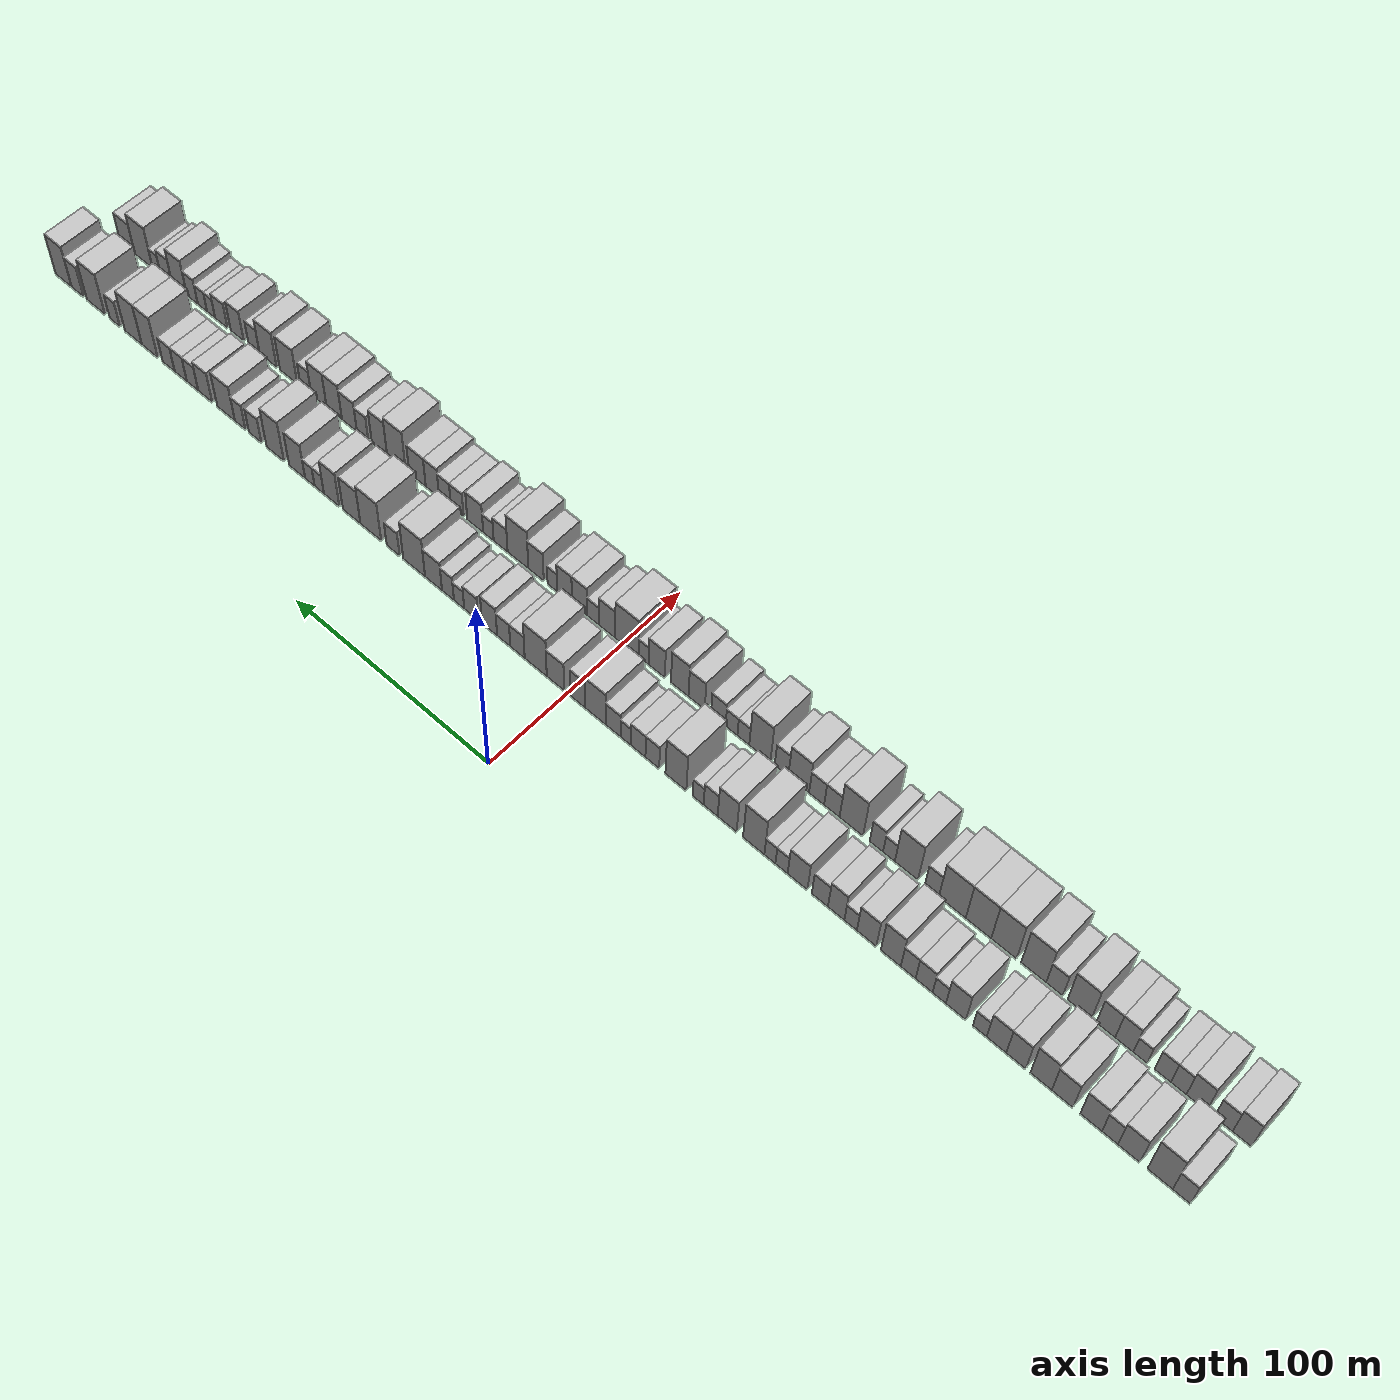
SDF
<sdf version="1.6">
 <world name="default">
  <scene>
   <sky><clouds><speed>12</speed></clouds></sky>
   <ambient>0.4 0.4 0.4 1</ambient>
   <background>0.7 0.7 0.7 1</background>
   <shadows>1</shadows>
  </scene>
  <gravity>0 0 -9.8066</gravity>
  <magnetic_field>6e-06 2.3e-05 -4.2e-05</magnetic_field>
  <physics default="0" name="default_physics" type="ode">
   <ode>
    <solver>
     <type>quick</type>
     <iters>10</iters>
     <sor>1.0</sor>
     <use_dynamic_moi_rescaling>0</use_dynamic_moi_rescaling>
    </solver>
    <constraints>
     <cfm>0</cfm>
     <erp>0.2</erp>
     <contact_max_correcting_vel>100</contact_max_correcting_vel>
     <contact_surface_layer>0.001</contact_surface_layer>
    </constraints>
   </ode>
   <max_step_size>0.004</max_step_size>
   <real_time_factor>1</real_time_factor>
   <real_time_update_rate>250</real_time_update_rate>
  </physics>
  <light name="sun" type="directional">
   <pose>0 0 10 0 0 0</pose>
   <diffuse>0.8 0.8 0.8 1</diffuse>
   <specular>0.2 0.2 0.2 1</specular>
   <attenuation>
    <range>1000</range>
    <constant>0.9</constant>
    <linear>0.01</linear>
    <quadratic>0.001</quadratic>
   </attenuation>
   <direction>-0.5 0.1 -0.9</direction>
  </light>
  <model name="building_1">
   <static>1</static>
   <pose>50.0000 -271.5159 0 0.000000 0.000000 0.000000</pose>
   <link name="link">
    <pose>0 0 7.50 0 0 0</pose>
    <collision name="collision"><geometry><box><size>20.0000 6.9682 15.0000</size></box></geometry></collision>
    <visual name="visual">
     <cast_shadows>0</cast_shadows>
     <geometry><box><size>20.0000 6.9682 15.0000</size></box></geometry>
     <material>
      <script>
       <uri>model://HANNAS_wall/materials/scripts</uri>
       <uri>model://HANNAS_wall/materials/textures</uri>
       <name>vrc/HANNAS_wall</name>
      </script>
     </material>
    </visual>
   </link>
  </model>
  <model name="building_2">
   <static>1</static>
   <pose>50.0000 -263.0658 0 0.000000 0.000000 0.000000</pose>
   <link name="link">
    <pose>0 0 12.00 0 0 0</pose>
    <collision name="collision"><geometry><box><size>20.0000 9.9319 24.0000</size></box></geometry></collision>
    <visual name="visual">
     <cast_shadows>0</cast_shadows>
     <geometry><box><size>20.0000 9.9319 24.0000</size></box></geometry>
     <material>
      <script>
       <uri>model://HANNAS_wall/materials/scripts</uri>
       <uri>model://HANNAS_wall/materials/textures</uri>
       <name>vrc/HANNAS_wall</name>
      </script>
     </material>
    </visual>
   </link>
  </model>
  <model name="building_3">
   <static>1</static>
   <pose>50.0000 -250.7267 0 0.000000 0.000000 0.000000</pose>
   <link name="link">
    <pose>0 0 9.00 0 0 0</pose>
    <collision name="collision"><geometry><box><size>20.0000 8.7463 18.0000</size></box></geometry></collision>
    <visual name="visual">
     <cast_shadows>0</cast_shadows>
     <geometry><box><size>20.0000 8.7463 18.0000</size></box></geometry>
     <material>
      <script>
       <uri>model://HANNAS_wall/materials/scripts</uri>
       <uri>model://HANNAS_wall/materials/textures</uri>
       <name>vrc/HANNAS_wall</name>
      </script>
     </material>
    </visual>
   </link>
  </model>
  <model name="building_4">
   <static>1</static>
   <pose>50.0000 -243.1369 0 0.000000 0.000000 0.000000</pose>
   <link name="link">
    <pose>0 0 7.50 0 0 0</pose>
    <collision name="collision"><geometry><box><size>20.0000 6.4332 15.0000</size></box></geometry></collision>
    <visual name="visual">
     <cast_shadows>0</cast_shadows>
     <geometry><box><size>20.0000 6.4332 15.0000</size></box></geometry>
     <material>
      <script>
       <uri>model://HANNAS_wall/materials/scripts</uri>
       <uri>model://HANNAS_wall/materials/textures</uri>
       <name>vrc/HANNAS_wall</name>
      </script>
     </material>
    </visual>
   </link>
  </model>
  <model name="building_5">
   <static>1</static>
   <pose>50.0000 -235.5371 0 0.000000 0.000000 0.000000</pose>
   <link name="link">
    <pose>0 0 9.00 0 0 0</pose>
    <collision name="collision"><geometry><box><size>20.0000 8.7665 18.0000</size></box></geometry></collision>
    <visual name="visual">
     <cast_shadows>0</cast_shadows>
     <geometry><box><size>20.0000 8.7665 18.0000</size></box></geometry>
     <material>
      <script>
       <uri>model://HANNAS_wall/materials/scripts</uri>
       <uri>model://HANNAS_wall/materials/textures</uri>
       <name>vrc/HANNAS_wall</name>
      </script>
     </material>
    </visual>
   </link>
  </model>
  <model name="building_6">
   <static>1</static>
   <pose>50.0000 -223.8168 0 0.000000 0.000000 0.000000</pose>
   <link name="link">
    <pose>0 0 9.00 0 0 0</pose>
    <collision name="collision"><geometry><box><size>20.0000 8.6742 18.0000</size></box></geometry></collision>
    <visual name="visual">
     <cast_shadows>0</cast_shadows>
     <geometry><box><size>20.0000 8.6742 18.0000</size></box></geometry>
     <material>
      <script>
       <uri>model://HANNAS_wall/materials/scripts</uri>
       <uri>model://HANNAS_wall/materials/textures</uri>
       <name>vrc/HANNAS_wall</name>
      </script>
     </material>
    </visual>
   </link>
  </model>
  <model name="building_7">
   <static>1</static>
   <pose>50.0000 -215.0911 0 0.000000 0.000000 0.000000</pose>
   <link name="link">
    <pose>0 0 10.50 0 0 0</pose>
    <collision name="collision"><geometry><box><size>20.0000 8.7772 21.0000</size></box></geometry></collision>
    <visual name="visual">
     <cast_shadows>0</cast_shadows>
     <geometry><box><size>20.0000 8.7772 21.0000</size></box></geometry>
     <material>
      <script>
       <uri>model://HANNAS_wall/materials/scripts</uri>
       <uri>model://HANNAS_wall/materials/textures</uri>
       <name>vrc/HANNAS_wall</name>
      </script>
     </material>
    </visual>
   </link>
  </model>
  <model name="building_8">
   <static>1</static>
   <pose>50.0000 -204.6598 0 0.000000 0.000000 0.000000</pose>
   <link name="link">
    <pose>0 0 9.00 0 0 0</pose>
    <collision name="collision"><geometry><box><size>20.0000 8.0854 18.0000</size></box></geometry></collision>
    <visual name="visual">
     <cast_shadows>0</cast_shadows>
     <geometry><box><size>20.0000 8.0854 18.0000</size></box></geometry>
     <material>
      <script>
       <uri>model://HANNAS_wall/materials/scripts</uri>
       <uri>model://HANNAS_wall/materials/textures</uri>
       <name>vrc/HANNAS_wall</name>
      </script>
     </material>
    </visual>
   </link>
  </model>
  <model name="building_9">
   <static>1</static>
   <pose>50.0000 -196.5052 0 0.000000 0.000000 0.000000</pose>
   <link name="link">
    <pose>0 0 9.00 0 0 0</pose>
    <collision name="collision"><geometry><box><size>20.0000 8.2237 18.0000</size></box></geometry></collision>
    <visual name="visual">
     <cast_shadows>0</cast_shadows>
     <geometry><box><size>20.0000 8.2237 18.0000</size></box></geometry>
     <material>
      <script>
       <uri>model://HANNAS_wall/materials/scripts</uri>
       <uri>model://HANNAS_wall/materials/textures</uri>
       <name>vrc/HANNAS_wall</name>
      </script>
     </material>
    </visual>
   </link>
  </model>
  <model name="building_10">
   <static>1</static>
   <pose>50.0000 -189.5027 0 0.000000 0.000000 0.000000</pose>
   <link name="link">
    <pose>0 0 6.00 0 0 0</pose>
    <collision name="collision"><geometry><box><size>20.0000 5.7813 12.0000</size></box></geometry></collision>
    <visual name="visual">
     <cast_shadows>0</cast_shadows>
     <geometry><box><size>20.0000 5.7813 12.0000</size></box></geometry>
     <material>
      <script>
       <uri>model://HANNAS_wall/materials/scripts</uri>
       <uri>model://HANNAS_wall/materials/textures</uri>
       <name>vrc/HANNAS_wall</name>
      </script>
     </material>
    </visual>
   </link>
  </model>
  <model name="building_11">
   <static>1</static>
   <pose>50.0000 -179.3486 0 0.000000 0.000000 0.000000</pose>
   <link name="link">
    <pose>0 0 9.00 0 0 0</pose>
    <collision name="collision"><geometry><box><size>20.0000 8.5268 18.0000</size></box></geometry></collision>
    <visual name="visual">
     <cast_shadows>0</cast_shadows>
     <geometry><box><size>20.0000 8.5268 18.0000</size></box></geometry>
     <material>
      <script>
       <uri>model://HANNAS_wall/materials/scripts</uri>
       <uri>model://HANNAS_wall/materials/textures</uri>
       <name>vrc/HANNAS_wall</name>
      </script>
     </material>
    </visual>
   </link>
  </model>
  <model name="building_12">
   <static>1</static>
   <pose>50.0000 -172.2277 0 0.000000 0.000000 0.000000</pose>
   <link name="link">
    <pose>0 0 6.00 0 0 0</pose>
    <collision name="collision"><geometry><box><size>20.0000 5.7151 12.0000</size></box></geometry></collision>
    <visual name="visual">
     <cast_shadows>0</cast_shadows>
     <geometry><box><size>20.0000 5.7151 12.0000</size></box></geometry>
     <material>
      <script>
       <uri>model://HANNAS_wall/materials/scripts</uri>
       <uri>model://HANNAS_wall/materials/textures</uri>
       <name>vrc/HANNAS_wall</name>
      </script>
     </material>
    </visual>
   </link>
  </model>
  <model name="building_13">
   <static>1</static>
   <pose>50.0000 -165.6933 0 0.000000 0.000000 0.000000</pose>
   <link name="link">
    <pose>0 0 7.50 0 0 0</pose>
    <collision name="collision"><geometry><box><size>20.0000 7.3537 15.0000</size></box></geometry></collision>
    <visual name="visual">
     <cast_shadows>0</cast_shadows>
     <geometry><box><size>20.0000 7.3537 15.0000</size></box></geometry>
     <material>
      <script>
       <uri>model://HANNAS_wall/materials/scripts</uri>
       <uri>model://HANNAS_wall/materials/textures</uri>
       <name>vrc/HANNAS_wall</name>
      </script>
     </material>
    </visual>
   </link>
  </model>
  <model name="building_14">
   <static>1</static>
   <pose>50.0000 -158.8166 0 0.000000 0.000000 0.000000</pose>
   <link name="link">
    <pose>0 0 7.50 0 0 0</pose>
    <collision name="collision"><geometry><box><size>20.0000 6.3997 15.0000</size></box></geometry></collision>
    <visual name="visual">
     <cast_shadows>0</cast_shadows>
     <geometry><box><size>20.0000 6.3997 15.0000</size></box></geometry>
     <material>
      <script>
       <uri>model://HANNAS_wall/materials/scripts</uri>
       <uri>model://HANNAS_wall/materials/textures</uri>
       <name>vrc/HANNAS_wall</name>
      </script>
     </material>
    </visual>
   </link>
  </model>
  <model name="building_15">
   <static>1</static>
   <pose>50.0000 -151.2310 0 0.000000 0.000000 0.000000</pose>
   <link name="link">
    <pose>0 0 10.50 0 0 0</pose>
    <collision name="collision"><geometry><box><size>20.0000 8.7715 21.0000</size></box></geometry></collision>
    <visual name="visual">
     <cast_shadows>0</cast_shadows>
     <geometry><box><size>20.0000 8.7715 21.0000</size></box></geometry>
     <material>
      <script>
       <uri>model://HANNAS_wall/materials/scripts</uri>
       <uri>model://HANNAS_wall/materials/textures</uri>
       <name>vrc/HANNAS_wall</name>
      </script>
     </material>
    </visual>
   </link>
  </model>
  <model name="building_16">
   <static>1</static>
   <pose>50.0000 -140.5599 0 0.000000 0.000000 0.000000</pose>
   <link name="link">
    <pose>0 0 9.00 0 0 0</pose>
    <collision name="collision"><geometry><box><size>20.0000 8.5708 18.0000</size></box></geometry></collision>
    <visual name="visual">
     <cast_shadows>0</cast_shadows>
     <geometry><box><size>20.0000 8.5708 18.0000</size></box></geometry>
     <material>
      <script>
       <uri>model://HANNAS_wall/materials/scripts</uri>
       <uri>model://HANNAS_wall/materials/textures</uri>
       <name>vrc/HANNAS_wall</name>
      </script>
     </material>
    </visual>
   </link>
  </model>
  <model name="building_17">
   <static>1</static>
   <pose>50.0000 -133.4870 0 0.000000 0.000000 0.000000</pose>
   <link name="link">
    <pose>0 0 6.00 0 0 0</pose>
    <collision name="collision"><geometry><box><size>20.0000 5.5748 12.0000</size></box></geometry></collision>
    <visual name="visual">
     <cast_shadows>0</cast_shadows>
     <geometry><box><size>20.0000 5.5748 12.0000</size></box></geometry>
     <material>
      <script>
       <uri>model://HANNAS_wall/materials/scripts</uri>
       <uri>model://HANNAS_wall/materials/textures</uri>
       <name>vrc/HANNAS_wall</name>
      </script>
     </material>
    </visual>
   </link>
  </model>
  <model name="building_18">
   <static>1</static>
   <pose>50.0000 -127.0307 0 0.000000 0.000000 0.000000</pose>
   <link name="link">
    <pose>0 0 9.00 0 0 0</pose>
    <collision name="collision"><geometry><box><size>20.0000 7.3379 18.0000</size></box></geometry></collision>
    <visual name="visual">
     <cast_shadows>0</cast_shadows>
     <geometry><box><size>20.0000 7.3379 18.0000</size></box></geometry>
     <material>
      <script>
       <uri>model://HANNAS_wall/materials/scripts</uri>
       <uri>model://HANNAS_wall/materials/textures</uri>
       <name>vrc/HANNAS_wall</name>
      </script>
     </material>
    </visual>
   </link>
  </model>
  <model name="building_19">
   <static>1</static>
   <pose>50.0000 -119.7201 0 0.000000 0.000000 0.000000</pose>
   <link name="link">
    <pose>0 0 7.50 0 0 0</pose>
    <collision name="collision"><geometry><box><size>20.0000 7.2834 15.0000</size></box></geometry></collision>
    <visual name="visual">
     <cast_shadows>0</cast_shadows>
     <geometry><box><size>20.0000 7.2834 15.0000</size></box></geometry>
     <material>
      <script>
       <uri>model://HANNAS_wall/materials/scripts</uri>
       <uri>model://HANNAS_wall/materials/textures</uri>
       <name>vrc/HANNAS_wall</name>
      </script>
     </material>
    </visual>
   </link>
  </model>
  <model name="building_20">
   <static>1</static>
   <pose>50.0000 -109.5894 0 0.000000 0.000000 0.000000</pose>
   <link name="link">
    <pose>0 0 9.00 0 0 0</pose>
    <collision name="collision"><geometry><box><size>20.0000 8.9779 18.0000</size></box></geometry></collision>
    <visual name="visual">
     <cast_shadows>0</cast_shadows>
     <geometry><box><size>20.0000 8.9779 18.0000</size></box></geometry>
     <material>
      <script>
       <uri>model://HANNAS_wall/materials/scripts</uri>
       <uri>model://HANNAS_wall/materials/textures</uri>
       <name>vrc/HANNAS_wall</name>
      </script>
     </material>
    </visual>
   </link>
  </model>
  <model name="building_21">
   <static>1</static>
   <pose>50.0000 -102.2996 0 0.000000 0.000000 0.000000</pose>
   <link name="link">
    <pose>0 0 6.00 0 0 0</pose>
    <collision name="collision"><geometry><box><size>20.0000 5.6018 12.0000</size></box></geometry></collision>
    <visual name="visual">
     <cast_shadows>0</cast_shadows>
     <geometry><box><size>20.0000 5.6018 12.0000</size></box></geometry>
     <material>
      <script>
       <uri>model://HANNAS_wall/materials/scripts</uri>
       <uri>model://HANNAS_wall/materials/textures</uri>
       <name>vrc/HANNAS_wall</name>
      </script>
     </material>
    </visual>
   </link>
  </model>
  <model name="building_22">
   <static>1</static>
   <pose>50.0000 -96.9715 0 0.000000 0.000000 0.000000</pose>
   <link name="link">
    <pose>0 0 6.00 0 0 0</pose>
    <collision name="collision"><geometry><box><size>20.0000 5.0544 12.0000</size></box></geometry></collision>
    <visual name="visual">
     <cast_shadows>0</cast_shadows>
     <geometry><box><size>20.0000 5.0544 12.0000</size></box></geometry>
     <material>
      <script>
       <uri>model://HANNAS_wall/materials/scripts</uri>
       <uri>model://HANNAS_wall/materials/textures</uri>
       <name>vrc/HANNAS_wall</name>
      </script>
     </material>
    </visual>
   </link>
  </model>
  <model name="building_23">
   <static>1</static>
   <pose>50.0000 -89.5114 0 0.000000 0.000000 0.000000</pose>
   <link name="link">
    <pose>0 0 12.00 0 0 0</pose>
    <collision name="collision"><geometry><box><size>20.0000 9.8659 24.0000</size></box></geometry></collision>
    <visual name="visual">
     <cast_shadows>0</cast_shadows>
     <geometry><box><size>20.0000 9.8659 24.0000</size></box></geometry>
     <material>
      <script>
       <uri>model://HANNAS_wall/materials/scripts</uri>
       <uri>model://HANNAS_wall/materials/textures</uri>
       <name>vrc/HANNAS_wall</name>
      </script>
     </material>
    </visual>
   </link>
  </model>
  <model name="building_24">
   <static>1</static>
   <pose>50.0000 -77.1458 0 0.000000 0.000000 0.000000</pose>
   <link name="link">
    <pose>0 0 10.50 0 0 0</pose>
    <collision name="collision"><geometry><box><size>20.0000 8.8653 21.0000</size></box></geometry></collision>
    <visual name="visual">
     <cast_shadows>0</cast_shadows>
     <geometry><box><size>20.0000 8.8653 21.0000</size></box></geometry>
     <material>
      <script>
       <uri>model://HANNAS_wall/materials/scripts</uri>
       <uri>model://HANNAS_wall/materials/textures</uri>
       <name>vrc/HANNAS_wall</name>
      </script>
     </material>
    </visual>
   </link>
  </model>
  <model name="building_25">
   <static>1</static>
   <pose>50.0000 -69.4078 0 0.000000 0.000000 0.000000</pose>
   <link name="link">
    <pose>0 0 7.50 0 0 0</pose>
    <collision name="collision"><geometry><box><size>20.0000 6.6107 15.0000</size></box></geometry></collision>
    <visual name="visual">
     <cast_shadows>0</cast_shadows>
     <geometry><box><size>20.0000 6.6107 15.0000</size></box></geometry>
     <material>
      <script>
       <uri>model://HANNAS_wall/materials/scripts</uri>
       <uri>model://HANNAS_wall/materials/textures</uri>
       <name>vrc/HANNAS_wall</name>
      </script>
     </material>
    </visual>
   </link>
  </model>
  <model name="building_26">
   <static>1</static>
   <pose>50.0000 -63.4971 0 0.000000 0.000000 0.000000</pose>
   <link name="link">
    <pose>0 0 6.00 0 0 0</pose>
    <collision name="collision"><geometry><box><size>20.0000 5.2108 12.0000</size></box></geometry></collision>
    <visual name="visual">
     <cast_shadows>0</cast_shadows>
     <geometry><box><size>20.0000 5.2108 12.0000</size></box></geometry>
     <material>
      <script>
       <uri>model://HANNAS_wall/materials/scripts</uri>
       <uri>model://HANNAS_wall/materials/textures</uri>
       <name>vrc/HANNAS_wall</name>
      </script>
     </material>
    </visual>
   </link>
  </model>
  <model name="building_27">
   <static>1</static>
   <pose>50.0000 -52.8952 0 0.000000 0.000000 0.000000</pose>
   <link name="link">
    <pose>0 0 12.00 0 0 0</pose>
    <collision name="collision"><geometry><box><size>20.0000 9.9930 24.0000</size></box></geometry></collision>
    <visual name="visual">
     <cast_shadows>0</cast_shadows>
     <geometry><box><size>20.0000 9.9930 24.0000</size></box></geometry>
     <material>
      <script>
       <uri>model://HANNAS_wall/materials/scripts</uri>
       <uri>model://HANNAS_wall/materials/textures</uri>
       <name>vrc/HANNAS_wall</name>
      </script>
     </material>
    </visual>
   </link>
  </model>
  <model name="building_28">
   <static>1</static>
   <pose>50.0000 -41.5784 0 0.000000 0.000000 0.000000</pose>
   <link name="link">
    <pose>0 0 7.50 0 0 0</pose>
    <collision name="collision"><geometry><box><size>20.0000 6.6407 15.0000</size></box></geometry></collision>
    <visual name="visual">
     <cast_shadows>0</cast_shadows>
     <geometry><box><size>20.0000 6.6407 15.0000</size></box></geometry>
     <material>
      <script>
       <uri>model://HANNAS_wall/materials/scripts</uri>
       <uri>model://HANNAS_wall/materials/textures</uri>
       <name>vrc/HANNAS_wall</name>
      </script>
     </material>
    </visual>
   </link>
  </model>
  <model name="building_29">
   <static>1</static>
   <pose>50.0000 -34.6689 0 0.000000 0.000000 0.000000</pose>
   <link name="link">
    <pose>0 0 7.50 0 0 0</pose>
    <collision name="collision"><geometry><box><size>20.0000 7.1783 15.0000</size></box></geometry></collision>
    <visual name="visual">
     <cast_shadows>0</cast_shadows>
     <geometry><box><size>20.0000 7.1783 15.0000</size></box></geometry>
     <material>
      <script>
       <uri>model://HANNAS_wall/materials/scripts</uri>
       <uri>model://HANNAS_wall/materials/textures</uri>
       <name>vrc/HANNAS_wall</name>
      </script>
     </material>
    </visual>
   </link>
  </model>
  <model name="building_30">
   <static>1</static>
   <pose>50.0000 -28.6052 0 0.000000 0.000000 0.000000</pose>
   <link name="link">
    <pose>0 0 6.00 0 0 0</pose>
    <collision name="collision"><geometry><box><size>20.0000 4.9491 12.0000</size></box></geometry></collision>
    <visual name="visual">
     <cast_shadows>0</cast_shadows>
     <geometry><box><size>20.0000 4.9491 12.0000</size></box></geometry>
     <material>
      <script>
       <uri>model://HANNAS_wall/materials/scripts</uri>
       <uri>model://HANNAS_wall/materials/textures</uri>
       <name>vrc/HANNAS_wall</name>
      </script>
     </material>
    </visual>
   </link>
  </model>
  <model name="building_31">
   <static>1</static>
   <pose>50.0000 -22.5011 0 0.000000 0.000000 0.000000</pose>
   <link name="link">
    <pose>0 0 7.50 0 0 0</pose>
    <collision name="collision"><geometry><box><size>20.0000 7.2591 15.0000</size></box></geometry></collision>
    <visual name="visual">
     <cast_shadows>0</cast_shadows>
     <geometry><box><size>20.0000 7.2591 15.0000</size></box></geometry>
     <material>
      <script>
       <uri>model://HANNAS_wall/materials/scripts</uri>
       <uri>model://HANNAS_wall/materials/textures</uri>
       <name>vrc/HANNAS_wall</name>
      </script>
     </material>
    </visual>
   </link>
  </model>
  <model name="building_32">
   <static>1</static>
   <pose>50.0000 -13.8042 0 0.000000 0.000000 0.000000</pose>
   <link name="link">
    <pose>0 0 10.50 0 0 0</pose>
    <collision name="collision"><geometry><box><size>20.0000 10.1348 21.0000</size></box></geometry></collision>
    <visual name="visual">
     <cast_shadows>0</cast_shadows>
     <geometry><box><size>20.0000 10.1348 21.0000</size></box></geometry>
     <material>
      <script>
       <uri>model://HANNAS_wall/materials/scripts</uri>
       <uri>model://HANNAS_wall/materials/textures</uri>
       <name>vrc/HANNAS_wall</name>
      </script>
     </material>
    </visual>
   </link>
  </model>
  <model name="building_33">
   <static>1</static>
   <pose>50.0000 -4.9800 0 0.000000 0.000000 0.000000</pose>
   <link name="link">
    <pose>0 0 9.00 0 0 0</pose>
    <collision name="collision"><geometry><box><size>20.0000 7.5135 18.0000</size></box></geometry></collision>
    <visual name="visual">
     <cast_shadows>0</cast_shadows>
     <geometry><box><size>20.0000 7.5135 18.0000</size></box></geometry>
     <material>
      <script>
       <uri>model://HANNAS_wall/materials/scripts</uri>
       <uri>model://HANNAS_wall/materials/textures</uri>
       <name>vrc/HANNAS_wall</name>
      </script>
     </material>
    </visual>
   </link>
  </model>
  <model name="building_34">
   <static>1</static>
   <pose>50.0000 6.1473 0 0.000000 0.000000 0.000000</pose>
   <link name="link">
    <pose>0 0 9.00 0 0 0</pose>
    <collision name="collision"><geometry><box><size>20.0000 8.7410 18.0000</size></box></geometry></collision>
    <visual name="visual">
     <cast_shadows>0</cast_shadows>
     <geometry><box><size>20.0000 8.7410 18.0000</size></box></geometry>
     <material>
      <script>
       <uri>model://HANNAS_wall/materials/scripts</uri>
       <uri>model://HANNAS_wall/materials/textures</uri>
       <name>vrc/HANNAS_wall</name>
      </script>
     </material>
    </visual>
   </link>
  </model>
  <model name="building_35">
   <static>1</static>
   <pose>50.0000 16.1103 0 0.000000 0.000000 0.000000</pose>
   <link name="link">
    <pose>0 0 12.00 0 0 0</pose>
    <collision name="collision"><geometry><box><size>20.0000 11.1851 24.0000</size></box></geometry></collision>
    <visual name="visual">
     <cast_shadows>0</cast_shadows>
     <geometry><box><size>20.0000 11.1851 24.0000</size></box></geometry>
     <material>
      <script>
       <uri>model://HANNAS_wall/materials/scripts</uri>
       <uri>model://HANNAS_wall/materials/textures</uri>
       <name>vrc/HANNAS_wall</name>
      </script>
     </material>
    </visual>
   </link>
  </model>
  <model name="building_36">
   <static>1</static>
   <pose>50.0000 25.3792 0 0.000000 0.000000 0.000000</pose>
   <link name="link">
    <pose>0 0 7.50 0 0 0</pose>
    <collision name="collision"><geometry><box><size>20.0000 7.3526 15.0000</size></box></geometry></collision>
    <visual name="visual">
     <cast_shadows>0</cast_shadows>
     <geometry><box><size>20.0000 7.3526 15.0000</size></box></geometry>
     <material>
      <script>
       <uri>model://HANNAS_wall/materials/scripts</uri>
       <uri>model://HANNAS_wall/materials/textures</uri>
       <name>vrc/HANNAS_wall</name>
      </script>
     </material>
    </visual>
   </link>
  </model>
  <model name="building_37">
   <static>1</static>
   <pose>50.0000 32.4388 0 0.000000 0.000000 0.000000</pose>
   <link name="link">
    <pose>0 0 7.50 0 0 0</pose>
    <collision name="collision"><geometry><box><size>20.0000 6.7667 15.0000</size></box></geometry></collision>
    <visual name="visual">
     <cast_shadows>0</cast_shadows>
     <geometry><box><size>20.0000 6.7667 15.0000</size></box></geometry>
     <material>
      <script>
       <uri>model://HANNAS_wall/materials/scripts</uri>
       <uri>model://HANNAS_wall/materials/textures</uri>
       <name>vrc/HANNAS_wall</name>
      </script>
     </material>
    </visual>
   </link>
  </model>
  <model name="building_38">
   <static>1</static>
   <pose>50.0000 39.7253 0 0.000000 0.000000 0.000000</pose>
   <link name="link">
    <pose>0 0 9.00 0 0 0</pose>
    <collision name="collision"><geometry><box><size>20.0000 7.8064 18.0000</size></box></geometry></collision>
    <visual name="visual">
     <cast_shadows>0</cast_shadows>
     <geometry><box><size>20.0000 7.8064 18.0000</size></box></geometry>
     <material>
      <script>
       <uri>model://HANNAS_wall/materials/scripts</uri>
       <uri>model://HANNAS_wall/materials/textures</uri>
       <name>vrc/HANNAS_wall</name>
      </script>
     </material>
    </visual>
   </link>
  </model>
  <model name="building_39">
   <static>1</static>
   <pose>50.0000 49.2765 0 0.000000 0.000000 0.000000</pose>
   <link name="link">
    <pose>0 0 7.50 0 0 0</pose>
    <collision name="collision"><geometry><box><size>20.0000 7.2959 15.0000</size></box></geometry></collision>
    <visual name="visual">
     <cast_shadows>0</cast_shadows>
     <geometry><box><size>20.0000 7.2959 15.0000</size></box></geometry>
     <material>
      <script>
       <uri>model://HANNAS_wall/materials/scripts</uri>
       <uri>model://HANNAS_wall/materials/textures</uri>
       <name>vrc/HANNAS_wall</name>
      </script>
     </material>
    </visual>
   </link>
  </model>
  <model name="building_40">
   <static>1</static>
   <pose>50.0000 55.6252 0 0.000000 0.000000 0.000000</pose>
   <link name="link">
    <pose>0 0 6.00 0 0 0</pose>
    <collision name="collision"><geometry><box><size>20.0000 5.4015 12.0000</size></box></geometry></collision>
    <visual name="visual">
     <cast_shadows>0</cast_shadows>
     <geometry><box><size>20.0000 5.4015 12.0000</size></box></geometry>
     <material>
      <script>
       <uri>model://HANNAS_wall/materials/scripts</uri>
       <uri>model://HANNAS_wall/materials/textures</uri>
       <name>vrc/HANNAS_wall</name>
      </script>
     </material>
    </visual>
   </link>
  </model>
  <model name="building_41">
   <static>1</static>
   <pose>50.0000 61.4513 0 0.000000 0.000000 0.000000</pose>
   <link name="link">
    <pose>0 0 7.50 0 0 0</pose>
    <collision name="collision"><geometry><box><size>20.0000 6.2506 15.0000</size></box></geometry></collision>
    <visual name="visual">
     <cast_shadows>0</cast_shadows>
     <geometry><box><size>20.0000 6.2506 15.0000</size></box></geometry>
     <material>
      <script>
       <uri>model://HANNAS_wall/materials/scripts</uri>
       <uri>model://HANNAS_wall/materials/textures</uri>
       <name>vrc/HANNAS_wall</name>
      </script>
     </material>
    </visual>
   </link>
  </model>
  <model name="building_42">
   <static>1</static>
   <pose>50.0000 69.0681 0 0.000000 0.000000 0.000000</pose>
   <link name="link">
    <pose>0 0 9.00 0 0 0</pose>
    <collision name="collision"><geometry><box><size>20.0000 8.9831 18.0000</size></box></geometry></collision>
    <visual name="visual">
     <cast_shadows>0</cast_shadows>
     <geometry><box><size>20.0000 8.9831 18.0000</size></box></geometry>
     <material>
      <script>
       <uri>model://HANNAS_wall/materials/scripts</uri>
       <uri>model://HANNAS_wall/materials/textures</uri>
       <name>vrc/HANNAS_wall</name>
      </script>
     </material>
    </visual>
   </link>
  </model>
  <model name="building_43">
   <static>1</static>
   <pose>50.0000 79.3780 0 0.000000 0.000000 0.000000</pose>
   <link name="link">
    <pose>0 0 12.00 0 0 0</pose>
    <collision name="collision"><geometry><box><size>20.0000 11.6367 24.0000</size></box></geometry></collision>
    <visual name="visual">
     <cast_shadows>0</cast_shadows>
     <geometry><box><size>20.0000 11.6367 24.0000</size></box></geometry>
     <material>
      <script>
       <uri>model://HANNAS_wall/materials/scripts</uri>
       <uri>model://HANNAS_wall/materials/textures</uri>
       <name>vrc/HANNAS_wall</name>
      </script>
     </material>
    </visual>
   </link>
  </model>
  <model name="building_44">
   <static>1</static>
   <pose>50.0000 90.6786 0 0.000000 0.000000 0.000000</pose>
   <link name="link">
    <pose>0 0 7.50 0 0 0</pose>
    <collision name="collision"><geometry><box><size>20.0000 6.9645 15.0000</size></box></geometry></collision>
    <visual name="visual">
     <cast_shadows>0</cast_shadows>
     <geometry><box><size>20.0000 6.9645 15.0000</size></box></geometry>
     <material>
      <script>
       <uri>model://HANNAS_wall/materials/scripts</uri>
       <uri>model://HANNAS_wall/materials/textures</uri>
       <name>vrc/HANNAS_wall</name>
      </script>
     </material>
    </visual>
   </link>
  </model>
  <model name="building_45">
   <static>1</static>
   <pose>50.0000 102.8169 0 0.000000 0.000000 0.000000</pose>
   <link name="link">
    <pose>0 0 12.00 0 0 0</pose>
    <collision name="collision"><geometry><box><size>20.0000 11.3121 24.0000</size></box></geometry></collision>
    <visual name="visual">
     <cast_shadows>0</cast_shadows>
     <geometry><box><size>20.0000 11.3121 24.0000</size></box></geometry>
     <material>
      <script>
       <uri>model://HANNAS_wall/materials/scripts</uri>
       <uri>model://HANNAS_wall/materials/textures</uri>
       <name>vrc/HANNAS_wall</name>
      </script>
     </material>
    </visual>
   </link>
  </model>
  <model name="building_46">
   <static>1</static>
   <pose>50.0000 113.2822 0 0.000000 0.000000 0.000000</pose>
   <link name="link">
    <pose>0 0 10.50 0 0 0</pose>
    <collision name="collision"><geometry><box><size>20.0000 9.6185 21.0000</size></box></geometry></collision>
    <visual name="visual">
     <cast_shadows>0</cast_shadows>
     <geometry><box><size>20.0000 9.6185 21.0000</size></box></geometry>
     <material>
      <script>
       <uri>model://HANNAS_wall/materials/scripts</uri>
       <uri>model://HANNAS_wall/materials/textures</uri>
       <name>vrc/HANNAS_wall</name>
      </script>
     </material>
    </visual>
   </link>
  </model>
  <model name="building_47">
   <static>1</static>
   <pose>50.0000 124.3903 0 0.000000 0.000000 0.000000</pose>
   <link name="link">
    <pose>0 0 10.50 0 0 0</pose>
    <collision name="collision"><geometry><box><size>20.0000 8.5976 21.0000</size></box></geometry></collision>
    <visual name="visual">
     <cast_shadows>0</cast_shadows>
     <geometry><box><size>20.0000 8.5976 21.0000</size></box></geometry>
     <material>
      <script>
       <uri>model://HANNAS_wall/materials/scripts</uri>
       <uri>model://HANNAS_wall/materials/textures</uri>
       <name>vrc/HANNAS_wall</name>
      </script>
     </material>
    </visual>
   </link>
  </model>
  <model name="building_48">
   <static>1</static>
   <pose>50.0000 131.2756 0 0.000000 0.000000 0.000000</pose>
   <link name="link">
    <pose>0 0 6.00 0 0 0</pose>
    <collision name="collision"><geometry><box><size>20.0000 5.1731 12.0000</size></box></geometry></collision>
    <visual name="visual">
     <cast_shadows>0</cast_shadows>
     <geometry><box><size>20.0000 5.1731 12.0000</size></box></geometry>
     <material>
      <script>
       <uri>model://HANNAS_wall/materials/scripts</uri>
       <uri>model://HANNAS_wall/materials/textures</uri>
       <name>vrc/HANNAS_wall</name>
      </script>
     </material>
    </visual>
   </link>
  </model>
  <model name="building_49">
   <static>1</static>
   <pose>50.0000 136.5101 0 0.000000 0.000000 0.000000</pose>
   <link name="link">
    <pose>0 0 6.00 0 0 0</pose>
    <collision name="collision"><geometry><box><size>20.0000 5.2959 12.0000</size></box></geometry></collision>
    <visual name="visual">
     <cast_shadows>0</cast_shadows>
     <geometry><box><size>20.0000 5.2959 12.0000</size></box></geometry>
     <material>
      <script>
       <uri>model://HANNAS_wall/materials/scripts</uri>
       <uri>model://HANNAS_wall/materials/textures</uri>
       <name>vrc/HANNAS_wall</name>
      </script>
     </material>
    </visual>
   </link>
  </model>
  <model name="building_50">
   <static>1</static>
   <pose>50.0000 143.6692 0 0.000000 0.000000 0.000000</pose>
   <link name="link">
    <pose>0 0 10.50 0 0 0</pose>
    <collision name="collision"><geometry><box><size>20.0000 9.0223 21.0000</size></box></geometry></collision>
    <visual name="visual">
     <cast_shadows>0</cast_shadows>
     <geometry><box><size>20.0000 9.0223 21.0000</size></box></geometry>
     <material>
      <script>
       <uri>model://HANNAS_wall/materials/scripts</uri>
       <uri>model://HANNAS_wall/materials/textures</uri>
       <name>vrc/HANNAS_wall</name>
      </script>
     </material>
    </visual>
   </link>
  </model>
  <model name="building_51">
   <static>1</static>
   <pose>50.0000 156.0944 0 0.000000 0.000000 0.000000</pose>
   <link name="link">
    <pose>0 0 12.00 0 0 0</pose>
    <collision name="collision"><geometry><box><size>20.0000 9.8281 24.0000</size></box></geometry></collision>
    <visual name="visual">
     <cast_shadows>0</cast_shadows>
     <geometry><box><size>20.0000 9.8281 24.0000</size></box></geometry>
     <material>
      <script>
       <uri>model://HANNAS_wall/materials/scripts</uri>
       <uri>model://HANNAS_wall/materials/textures</uri>
       <name>vrc/HANNAS_wall</name>
      </script>
     </material>
    </visual>
   </link>
  </model>
  <model name="building_52">
   <static>1</static>
   <pose>50.0000 167.5904 0 0.000000 0.000000 0.000000</pose>
   <link name="link">
    <pose>0 0 7.50 0 0 0</pose>
    <collision name="collision"><geometry><box><size>20.0000 7.1639 15.0000</size></box></geometry></collision>
    <visual name="visual">
     <cast_shadows>0</cast_shadows>
     <geometry><box><size>20.0000 7.1639 15.0000</size></box></geometry>
     <material>
      <script>
       <uri>model://HANNAS_wall/materials/scripts</uri>
       <uri>model://HANNAS_wall/materials/textures</uri>
       <name>vrc/HANNAS_wall</name>
      </script>
     </material>
    </visual>
   </link>
  </model>
  <model name="building_53">
   <static>1</static>
   <pose>50.0000 176.2179 0 0.000000 0.000000 0.000000</pose>
   <link name="link">
    <pose>0 0 7.50 0 0 0</pose>
    <collision name="collision"><geometry><box><size>20.0000 6.0910 15.0000</size></box></geometry></collision>
    <visual name="visual">
     <cast_shadows>0</cast_shadows>
     <geometry><box><size>20.0000 6.0910 15.0000</size></box></geometry>
     <material>
      <script>
       <uri>model://HANNAS_wall/materials/scripts</uri>
       <uri>model://HANNAS_wall/materials/textures</uri>
       <name>vrc/HANNAS_wall</name>
      </script>
     </material>
    </visual>
   </link>
  </model>
  <model name="building_54">
   <static>1</static>
   <pose>50.0000 184.3820 0 0.000000 0.000000 0.000000</pose>
   <link name="link">
    <pose>0 0 10.50 0 0 0</pose>
    <collision name="collision"><geometry><box><size>20.0000 10.2371 21.0000</size></box></geometry></collision>
    <visual name="visual">
     <cast_shadows>0</cast_shadows>
     <geometry><box><size>20.0000 10.2371 21.0000</size></box></geometry>
     <material>
      <script>
       <uri>model://HANNAS_wall/materials/scripts</uri>
       <uri>model://HANNAS_wall/materials/textures</uri>
       <name>vrc/HANNAS_wall</name>
      </script>
     </material>
    </visual>
   </link>
  </model>
  <model name="building_55">
   <static>1</static>
   <pose>50.0000 196.5752 0 0.000000 0.000000 0.000000</pose>
   <link name="link">
    <pose>0 0 9.00 0 0 0</pose>
    <collision name="collision"><geometry><box><size>20.0000 8.1494 18.0000</size></box></geometry></collision>
    <visual name="visual">
     <cast_shadows>0</cast_shadows>
     <geometry><box><size>20.0000 8.1494 18.0000</size></box></geometry>
     <material>
      <script>
       <uri>model://HANNAS_wall/materials/scripts</uri>
       <uri>model://HANNAS_wall/materials/textures</uri>
       <name>vrc/HANNAS_wall</name>
      </script>
     </material>
    </visual>
   </link>
  </model>
  <model name="building_56">
   <static>1</static>
   <pose>50.0000 204.0427 0 0.000000 0.000000 0.000000</pose>
   <link name="link">
    <pose>0 0 7.50 0 0 0</pose>
    <collision name="collision"><geometry><box><size>20.0000 6.7856 15.0000</size></box></geometry></collision>
    <visual name="visual">
     <cast_shadows>0</cast_shadows>
     <geometry><box><size>20.0000 6.7856 15.0000</size></box></geometry>
     <material>
      <script>
       <uri>model://HANNAS_wall/materials/scripts</uri>
       <uri>model://HANNAS_wall/materials/textures</uri>
       <name>vrc/HANNAS_wall</name>
      </script>
     </material>
    </visual>
   </link>
  </model>
  <model name="building_57">
   <static>1</static>
   <pose>50.0000 211.0409 0 0.000000 0.000000 0.000000</pose>
   <link name="link">
    <pose>0 0 7.50 0 0 0</pose>
    <collision name="collision"><geometry><box><size>20.0000 7.2108 15.0000</size></box></geometry></collision>
    <visual name="visual">
     <cast_shadows>0</cast_shadows>
     <geometry><box><size>20.0000 7.2108 15.0000</size></box></geometry>
     <material>
      <script>
       <uri>model://HANNAS_wall/materials/scripts</uri>
       <uri>model://HANNAS_wall/materials/textures</uri>
       <name>vrc/HANNAS_wall</name>
      </script>
     </material>
    </visual>
   </link>
  </model>
  <model name="building_58">
   <static>1</static>
   <pose>50.0000 218.2572 0 0.000000 0.000000 0.000000</pose>
   <link name="link">
    <pose>0 0 7.50 0 0 0</pose>
    <collision name="collision"><geometry><box><size>20.0000 7.2218 15.0000</size></box></geometry></collision>
    <visual name="visual">
     <cast_shadows>0</cast_shadows>
     <geometry><box><size>20.0000 7.2218 15.0000</size></box></geometry>
     <material>
      <script>
       <uri>model://HANNAS_wall/materials/scripts</uri>
       <uri>model://HANNAS_wall/materials/textures</uri>
       <name>vrc/HANNAS_wall</name>
      </script>
     </material>
    </visual>
   </link>
  </model>
  <model name="building_59">
   <static>1</static>
   <pose>50.0000 229.6732 0 0.000000 0.000000 0.000000</pose>
   <link name="link">
    <pose>0 0 12.00 0 0 0</pose>
    <collision name="collision"><geometry><box><size>20.0000 9.6101 24.0000</size></box></geometry></collision>
    <visual name="visual">
     <cast_shadows>0</cast_shadows>
     <geometry><box><size>20.0000 9.6101 24.0000</size></box></geometry>
     <material>
      <script>
       <uri>model://HANNAS_wall/materials/scripts</uri>
       <uri>model://HANNAS_wall/materials/textures</uri>
       <name>vrc/HANNAS_wall</name>
      </script>
     </material>
    </visual>
   </link>
  </model>
  <model name="building_60">
   <static>1</static>
   <pose>50.0000 239.6133 0 0.000000 0.000000 0.000000</pose>
   <link name="link">
    <pose>0 0 12.00 0 0 0</pose>
    <collision name="collision"><geometry><box><size>20.0000 10.2700 24.0000</size></box></geometry></collision>
    <visual name="visual">
     <cast_shadows>0</cast_shadows>
     <geometry><box><size>20.0000 10.2700 24.0000</size></box></geometry>
     <material>
      <script>
       <uri>model://HANNAS_wall/materials/scripts</uri>
       <uri>model://HANNAS_wall/materials/textures</uri>
       <name>vrc/HANNAS_wall</name>
      </script>
     </material>
    </visual>
   </link>
  </model>
  <model name="building_61">
   <static>1</static>
   <pose>50.0000 250.8751 0 0.000000 0.000000 0.000000</pose>
   <link name="link">
    <pose>0 0 7.50 0 0 0</pose>
    <collision name="collision"><geometry><box><size>20.0000 6.2536 15.0000</size></box></geometry></collision>
    <visual name="visual">
     <cast_shadows>0</cast_shadows>
     <geometry><box><size>20.0000 6.2536 15.0000</size></box></geometry>
     <material>
      <script>
       <uri>model://HANNAS_wall/materials/scripts</uri>
       <uri>model://HANNAS_wall/materials/textures</uri>
       <name>vrc/HANNAS_wall</name>
      </script>
     </material>
    </visual>
   </link>
  </model>
  <model name="building_62">
   <static>1</static>
   <pose>50.0000 262.5976 0 0.000000 0.000000 0.000000</pose>
   <link name="link">
    <pose>0 0 12.00 0 0 0</pose>
    <collision name="collision"><geometry><box><size>20.0000 11.1915 24.0000</size></box></geometry></collision>
    <visual name="visual">
     <cast_shadows>0</cast_shadows>
     <geometry><box><size>20.0000 11.1915 24.0000</size></box></geometry>
     <material>
      <script>
       <uri>model://HANNAS_wall/materials/scripts</uri>
       <uri>model://HANNAS_wall/materials/textures</uri>
       <name>vrc/HANNAS_wall</name>
      </script>
     </material>
    </visual>
   </link>
  </model>
  <model name="building_63">
   <static>1</static>
   <pose>50.0000 273.9101 0 0.000000 0.000000 0.000000</pose>
   <link name="link">
    <pose>0 0 9.00 0 0 0</pose>
    <collision name="collision"><geometry><box><size>20.0000 7.4335 18.0000</size></box></geometry></collision>
    <visual name="visual">
     <cast_shadows>0</cast_shadows>
     <geometry><box><size>20.0000 7.4335 18.0000</size></box></geometry>
     <material>
      <script>
       <uri>model://HANNAS_wall/materials/scripts</uri>
       <uri>model://HANNAS_wall/materials/textures</uri>
       <name>vrc/HANNAS_wall</name>
      </script>
     </material>
    </visual>
   </link>
  </model>
  <model name="building_64">
   <static>1</static>
   <pose>50.0000 282.6884 0 0.000000 0.000000 0.000000</pose>
   <link name="link">
    <pose>0 0 12.00 0 0 0</pose>
    <collision name="collision"><geometry><box><size>20.0000 10.1232 24.0000</size></box></geometry></collision>
    <visual name="visual">
     <cast_shadows>0</cast_shadows>
     <geometry><box><size>20.0000 10.1232 24.0000</size></box></geometry>
     <material>
      <script>
       <uri>model://HANNAS_wall/materials/scripts</uri>
       <uri>model://HANNAS_wall/materials/textures</uri>
       <name>vrc/HANNAS_wall</name>
      </script>
     </material>
    </visual>
   </link>
  </model>
  <model name="building_65">
   <static>1</static>
   <pose>79.0000 -274.2738 0 0.000000 0.000000 0.000000</pose>
   <link name="link">
    <pose>0 0 9.00 0 0 0</pose>
    <collision name="collision"><geometry><box><size>20.0000 7.4524 18.0000</size></box></geometry></collision>
    <visual name="visual">
     <cast_shadows>0</cast_shadows>
     <geometry><box><size>20.0000 7.4524 18.0000</size></box></geometry>
     <material>
      <script>
       <uri>model://HANNAS_wall/materials/scripts</uri>
       <uri>model://HANNAS_wall/materials/textures</uri>
       <name>vrc/HANNAS_wall</name>
      </script>
     </material>
    </visual>
   </link>
  </model>
  <model name="building_66">
   <static>1</static>
   <pose>79.0000 -266.9235 0 0.000000 0.000000 0.000000</pose>
   <link name="link">
    <pose>0 0 7.50 0 0 0</pose>
    <collision name="collision"><geometry><box><size>20.0000 7.2481 15.0000</size></box></geometry></collision>
    <visual name="visual">
     <cast_shadows>0</cast_shadows>
     <geometry><box><size>20.0000 7.2481 15.0000</size></box></geometry>
     <material>
      <script>
       <uri>model://HANNAS_wall/materials/scripts</uri>
       <uri>model://HANNAS_wall/materials/textures</uri>
       <name>vrc/HANNAS_wall</name>
      </script>
     </material>
    </visual>
   </link>
  </model>
  <model name="building_67">
   <static>1</static>
   <pose>79.0000 -256.2672 0 0.000000 0.000000 0.000000</pose>
   <link name="link">
    <pose>0 0 9.00 0 0 0</pose>
    <collision name="collision"><geometry><box><size>20.0000 8.0646 18.0000</size></box></geometry></collision>
    <visual name="visual">
     <cast_shadows>0</cast_shadows>
     <geometry><box><size>20.0000 8.0646 18.0000</size></box></geometry>
     <material>
      <script>
       <uri>model://HANNAS_wall/materials/scripts</uri>
       <uri>model://HANNAS_wall/materials/textures</uri>
       <name>vrc/HANNAS_wall</name>
      </script>
     </material>
    </visual>
   </link>
  </model>
  <model name="building_68">
   <static>1</static>
   <pose>79.0000 -249.1426 0 0.000000 0.000000 0.000000</pose>
   <link name="link">
    <pose>0 0 7.50 0 0 0</pose>
    <collision name="collision"><geometry><box><size>20.0000 6.1846 15.0000</size></box></geometry></collision>
    <visual name="visual">
     <cast_shadows>0</cast_shadows>
     <geometry><box><size>20.0000 6.1846 15.0000</size></box></geometry>
     <material>
      <script>
       <uri>model://HANNAS_wall/materials/scripts</uri>
       <uri>model://HANNAS_wall/materials/textures</uri>
       <name>vrc/HANNAS_wall</name>
      </script>
     </material>
    </visual>
   </link>
  </model>
  <model name="building_69">
   <static>1</static>
   <pose>79.0000 -242.7590 0 0.000000 0.000000 0.000000</pose>
   <link name="link">
    <pose>0 0 7.50 0 0 0</pose>
    <collision name="collision"><geometry><box><size>20.0000 6.5827 15.0000</size></box></geometry></collision>
    <visual name="visual">
     <cast_shadows>0</cast_shadows>
     <geometry><box><size>20.0000 6.5827 15.0000</size></box></geometry>
     <material>
      <script>
       <uri>model://HANNAS_wall/materials/scripts</uri>
       <uri>model://HANNAS_wall/materials/textures</uri>
       <name>vrc/HANNAS_wall</name>
      </script>
     </material>
    </visual>
   </link>
  </model>
  <model name="building_70">
   <static>1</static>
   <pose>79.0000 -233.6264 0 0.000000 0.000000 0.000000</pose>
   <link name="link">
    <pose>0 0 6.00 0 0 0</pose>
    <collision name="collision"><geometry><box><size>20.0000 5.6826 12.0000</size></box></geometry></collision>
    <visual name="visual">
     <cast_shadows>0</cast_shadows>
     <geometry><box><size>20.0000 5.6826 12.0000</size></box></geometry>
     <material>
      <script>
       <uri>model://HANNAS_wall/materials/scripts</uri>
       <uri>model://HANNAS_wall/materials/textures</uri>
       <name>vrc/HANNAS_wall</name>
      </script>
     </material>
    </visual>
   </link>
  </model>
  <model name="building_71">
   <static>1</static>
   <pose>79.0000 -227.0682 0 0.000000 0.000000 0.000000</pose>
   <link name="link">
    <pose>0 0 9.00 0 0 0</pose>
    <collision name="collision"><geometry><box><size>20.0000 7.4338 18.0000</size></box></geometry></collision>
    <visual name="visual">
     <cast_shadows>0</cast_shadows>
     <geometry><box><size>20.0000 7.4338 18.0000</size></box></geometry>
     <material>
      <script>
       <uri>model://HANNAS_wall/materials/scripts</uri>
       <uri>model://HANNAS_wall/materials/textures</uri>
       <name>vrc/HANNAS_wall</name>
      </script>
     </material>
    </visual>
   </link>
  </model>
  <model name="building_72">
   <static>1</static>
   <pose>79.0000 -219.4555 0 0.000000 0.000000 0.000000</pose>
   <link name="link">
    <pose>0 0 9.00 0 0 0</pose>
    <collision name="collision"><geometry><box><size>20.0000 7.7916 18.0000</size></box></geometry></collision>
    <visual name="visual">
     <cast_shadows>0</cast_shadows>
     <geometry><box><size>20.0000 7.7916 18.0000</size></box></geometry>
     <material>
      <script>
       <uri>model://HANNAS_wall/materials/scripts</uri>
       <uri>model://HANNAS_wall/materials/textures</uri>
       <name>vrc/HANNAS_wall</name>
      </script>
     </material>
    </visual>
   </link>
  </model>
  <model name="building_73">
   <static>1</static>
   <pose>79.0000 -208.5744 0 0.000000 0.000000 0.000000</pose>
   <link name="link">
    <pose>0 0 10.50 0 0 0</pose>
    <collision name="collision"><geometry><box><size>20.0000 9.9707 21.0000</size></box></geometry></collision>
    <visual name="visual">
     <cast_shadows>0</cast_shadows>
     <geometry><box><size>20.0000 9.9707 21.0000</size></box></geometry>
     <material>
      <script>
       <uri>model://HANNAS_wall/materials/scripts</uri>
       <uri>model://HANNAS_wall/materials/textures</uri>
       <name>vrc/HANNAS_wall</name>
      </script>
     </material>
    </visual>
   </link>
  </model>
  <model name="building_74">
   <static>1</static>
   <pose>79.0000 -198.1087 0 0.000000 0.000000 0.000000</pose>
   <link name="link">
    <pose>0 0 7.50 0 0 0</pose>
    <collision name="collision"><geometry><box><size>20.0000 6.9607 15.0000</size></box></geometry></collision>
    <visual name="visual">
     <cast_shadows>0</cast_shadows>
     <geometry><box><size>20.0000 6.9607 15.0000</size></box></geometry>
     <material>
      <script>
       <uri>model://HANNAS_wall/materials/scripts</uri>
       <uri>model://HANNAS_wall/materials/textures</uri>
       <name>vrc/HANNAS_wall</name>
      </script>
     </material>
    </visual>
   </link>
  </model>
  <model name="building_75">
   <static>1</static>
   <pose>79.0000 -189.3229 0 0.000000 0.000000 0.000000</pose>
   <link name="link">
    <pose>0 0 12.00 0 0 0</pose>
    <collision name="collision"><geometry><box><size>20.0000 10.6109 24.0000</size></box></geometry></collision>
    <visual name="visual">
     <cast_shadows>0</cast_shadows>
     <geometry><box><size>20.0000 10.6109 24.0000</size></box></geometry>
     <material>
      <script>
       <uri>model://HANNAS_wall/materials/scripts</uri>
       <uri>model://HANNAS_wall/materials/textures</uri>
       <name>vrc/HANNAS_wall</name>
      </script>
     </material>
    </visual>
   </link>
  </model>
  <model name="building_76">
   <static>1</static>
   <pose>79.0000 -176.5898 0 0.000000 0.000000 0.000000</pose>
   <link name="link">
    <pose>0 0 12.00 0 0 0</pose>
    <collision name="collision"><geometry><box><size>20.0000 10.8552 24.0000</size></box></geometry></collision>
    <visual name="visual">
     <cast_shadows>0</cast_shadows>
     <geometry><box><size>20.0000 10.8552 24.0000</size></box></geometry>
     <material>
      <script>
       <uri>model://HANNAS_wall/materials/scripts</uri>
       <uri>model://HANNAS_wall/materials/textures</uri>
       <name>vrc/HANNAS_wall</name>
      </script>
     </material>
    </visual>
   </link>
  </model>
  <model name="building_77">
   <static>1</static>
   <pose>79.0000 -165.6441 0 0.000000 0.000000 0.000000</pose>
   <link name="link">
    <pose>0 0 12.00 0 0 0</pose>
    <collision name="collision"><geometry><box><size>20.0000 11.0362 24.0000</size></box></geometry></collision>
    <visual name="visual">
     <cast_shadows>0</cast_shadows>
     <geometry><box><size>20.0000 11.0362 24.0000</size></box></geometry>
     <material>
      <script>
       <uri>model://HANNAS_wall/materials/scripts</uri>
       <uri>model://HANNAS_wall/materials/textures</uri>
       <name>vrc/HANNAS_wall</name>
      </script>
     </material>
    </visual>
   </link>
  </model>
  <model name="building_78">
   <static>1</static>
   <pose>79.0000 -154.2432 0 0.000000 0.000000 0.000000</pose>
   <link name="link">
    <pose>0 0 12.00 0 0 0</pose>
    <collision name="collision"><geometry><box><size>20.0000 11.7656 24.0000</size></box></geometry></collision>
    <visual name="visual">
     <cast_shadows>0</cast_shadows>
     <geometry><box><size>20.0000 11.7656 24.0000</size></box></geometry>
     <material>
      <script>
       <uri>model://HANNAS_wall/materials/scripts</uri>
       <uri>model://HANNAS_wall/materials/textures</uri>
       <name>vrc/HANNAS_wall</name>
      </script>
     </material>
    </visual>
   </link>
  </model>
  <model name="building_79">
   <static>1</static>
   <pose>79.0000 -145.2386 0 0.000000 0.000000 0.000000</pose>
   <link name="link">
    <pose>0 0 7.50 0 0 0</pose>
    <collision name="collision"><geometry><box><size>20.0000 6.2436 15.0000</size></box></geometry></collision>
    <visual name="visual">
     <cast_shadows>0</cast_shadows>
     <geometry><box><size>20.0000 6.2436 15.0000</size></box></geometry>
     <material>
      <script>
       <uri>model://HANNAS_wall/materials/scripts</uri>
       <uri>model://HANNAS_wall/materials/textures</uri>
       <name>vrc/HANNAS_wall</name>
      </script>
     </material>
    </visual>
   </link>
  </model>
  <model name="building_80">
   <static>1</static>
   <pose>79.0000 -133.9576 0 0.000000 0.000000 0.000000</pose>
   <link name="link">
    <pose>0 0 12.00 0 0 0</pose>
    <collision name="collision"><geometry><box><size>20.0000 10.3185 24.0000</size></box></geometry></collision>
    <visual name="visual">
     <cast_shadows>0</cast_shadows>
     <geometry><box><size>20.0000 10.3185 24.0000</size></box></geometry>
     <material>
      <script>
       <uri>model://HANNAS_wall/materials/scripts</uri>
       <uri>model://HANNAS_wall/materials/textures</uri>
       <name>vrc/HANNAS_wall</name>
      </script>
     </material>
    </visual>
   </link>
  </model>
  <model name="building_81">
   <static>1</static>
   <pose>79.0000 -126.1521 0 0.000000 0.000000 0.000000</pose>
   <link name="link">
    <pose>0 0 6.00 0 0 0</pose>
    <collision name="collision"><geometry><box><size>20.0000 5.2923 12.0000</size></box></geometry></collision>
    <visual name="visual">
     <cast_shadows>0</cast_shadows>
     <geometry><box><size>20.0000 5.2923 12.0000</size></box></geometry>
     <material>
      <script>
       <uri>model://HANNAS_wall/materials/scripts</uri>
       <uri>model://HANNAS_wall/materials/textures</uri>
       <name>vrc/HANNAS_wall</name>
      </script>
     </material>
    </visual>
   </link>
  </model>
  <model name="building_82">
   <static>1</static>
   <pose>79.0000 -120.4873 0 0.000000 0.000000 0.000000</pose>
   <link name="link">
    <pose>0 0 7.50 0 0 0</pose>
    <collision name="collision"><geometry><box><size>20.0000 6.0373 15.0000</size></box></geometry></collision>
    <visual name="visual">
     <cast_shadows>0</cast_shadows>
     <geometry><box><size>20.0000 6.0373 15.0000</size></box></geometry>
     <material>
      <script>
       <uri>model://HANNAS_wall/materials/scripts</uri>
       <uri>model://HANNAS_wall/materials/textures</uri>
       <name>vrc/HANNAS_wall</name>
      </script>
     </material>
    </visual>
   </link>
  </model>
  <model name="building_83">
   <static>1</static>
   <pose>79.0000 -109.1049 0 0.000000 0.000000 0.000000</pose>
   <link name="link">
    <pose>0 0 12.00 0 0 0</pose>
    <collision name="collision"><geometry><box><size>20.0000 10.7276 24.0000</size></box></geometry></collision>
    <visual name="visual">
     <cast_shadows>0</cast_shadows>
     <geometry><box><size>20.0000 10.7276 24.0000</size></box></geometry>
     <material>
      <script>
       <uri>model://HANNAS_wall/materials/scripts</uri>
       <uri>model://HANNAS_wall/materials/textures</uri>
       <name>vrc/HANNAS_wall</name>
      </script>
     </material>
    </visual>
   </link>
  </model>
  <model name="building_84">
   <static>1</static>
   <pose>79.0000 -100.1925 0 0.000000 0.000000 0.000000</pose>
   <link name="link">
    <pose>0 0 7.50 0 0 0</pose>
    <collision name="collision"><geometry><box><size>20.0000 7.0971 15.0000</size></box></geometry></collision>
    <visual name="visual">
     <cast_shadows>0</cast_shadows>
     <geometry><box><size>20.0000 7.0971 15.0000</size></box></geometry>
     <material>
      <script>
       <uri>model://HANNAS_wall/materials/scripts</uri>
       <uri>model://HANNAS_wall/materials/textures</uri>
       <name>vrc/HANNAS_wall</name>
      </script>
     </material>
    </visual>
   </link>
  </model>
  <model name="building_85">
   <static>1</static>
   <pose>79.0000 -93.1695 0 0.000000 0.000000 0.000000</pose>
   <link name="link">
    <pose>0 0 7.50 0 0 0</pose>
    <collision name="collision"><geometry><box><size>20.0000 6.9489 15.0000</size></box></geometry></collision>
    <visual name="visual">
     <cast_shadows>0</cast_shadows>
     <geometry><box><size>20.0000 6.9489 15.0000</size></box></geometry>
     <material>
      <script>
       <uri>model://HANNAS_wall/materials/scripts</uri>
       <uri>model://HANNAS_wall/materials/textures</uri>
       <name>vrc/HANNAS_wall</name>
      </script>
     </material>
    </visual>
   </link>
  </model>
  <model name="building_86">
   <static>1</static>
   <pose>79.0000 -84.8528 0 0.000000 0.000000 0.000000</pose>
   <link name="link">
    <pose>0 0 10.50 0 0 0</pose>
    <collision name="collision"><geometry><box><size>20.0000 9.6846 21.0000</size></box></geometry></collision>
    <visual name="visual">
     <cast_shadows>0</cast_shadows>
     <geometry><box><size>20.0000 9.6846 21.0000</size></box></geometry>
     <material>
      <script>
       <uri>model://HANNAS_wall/materials/scripts</uri>
       <uri>model://HANNAS_wall/materials/textures</uri>
       <name>vrc/HANNAS_wall</name>
      </script>
     </material>
    </visual>
   </link>
  </model>
  <model name="building_87">
   <static>1</static>
   <pose>79.0000 -76.8187 0 0.000000 0.000000 0.000000</pose>
   <link name="link">
    <pose>0 0 7.50 0 0 0</pose>
    <collision name="collision"><geometry><box><size>20.0000 6.3835 15.0000</size></box></geometry></collision>
    <visual name="visual">
     <cast_shadows>0</cast_shadows>
     <geometry><box><size>20.0000 6.3835 15.0000</size></box></geometry>
     <material>
      <script>
       <uri>model://HANNAS_wall/materials/scripts</uri>
       <uri>model://HANNAS_wall/materials/textures</uri>
       <name>vrc/HANNAS_wall</name>
      </script>
     </material>
    </visual>
   </link>
  </model>
  <model name="building_88">
   <static>1</static>
   <pose>79.0000 -66.6269 0 0.000000 0.000000 0.000000</pose>
   <link name="link">
    <pose>0 0 12.00 0 0 0</pose>
    <collision name="collision"><geometry><box><size>20.0000 10.0001 24.0000</size></box></geometry></collision>
    <visual name="visual">
     <cast_shadows>0</cast_shadows>
     <geometry><box><size>20.0000 10.0001 24.0000</size></box></geometry>
     <material>
      <script>
       <uri>model://HANNAS_wall/materials/scripts</uri>
       <uri>model://HANNAS_wall/materials/textures</uri>
       <name>vrc/HANNAS_wall</name>
      </script>
     </material>
    </visual>
   </link>
  </model>
  <model name="building_89">
   <static>1</static>
   <pose>79.0000 -58.7938 0 0.000000 0.000000 0.000000</pose>
   <link name="link">
    <pose>0 0 6.00 0 0 0</pose>
    <collision name="collision"><geometry><box><size>20.0000 5.6661 12.0000</size></box></geometry></collision>
    <visual name="visual">
     <cast_shadows>0</cast_shadows>
     <geometry><box><size>20.0000 5.6661 12.0000</size></box></geometry>
     <material>
      <script>
       <uri>model://HANNAS_wall/materials/scripts</uri>
       <uri>model://HANNAS_wall/materials/textures</uri>
       <name>vrc/HANNAS_wall</name>
      </script>
     </material>
    </visual>
   </link>
  </model>
  <model name="building_90">
   <static>1</static>
   <pose>79.0000 -53.1214 0 0.000000 0.000000 0.000000</pose>
   <link name="link">
    <pose>0 0 6.00 0 0 0</pose>
    <collision name="collision"><geometry><box><size>20.0000 5.6786 12.0000</size></box></geometry></collision>
    <visual name="visual">
     <cast_shadows>0</cast_shadows>
     <geometry><box><size>20.0000 5.6786 12.0000</size></box></geometry>
     <material>
      <script>
       <uri>model://HANNAS_wall/materials/scripts</uri>
       <uri>model://HANNAS_wall/materials/textures</uri>
       <name>vrc/HANNAS_wall</name>
      </script>
     </material>
    </visual>
   </link>
  </model>
  <model name="building_91">
   <static>1</static>
   <pose>79.0000 -46.7652 0 0.000000 0.000000 0.000000</pose>
   <link name="link">
    <pose>0 0 7.50 0 0 0</pose>
    <collision name="collision"><geometry><box><size>20.0000 7.0340 15.0000</size></box></geometry></collision>
    <visual name="visual">
     <cast_shadows>0</cast_shadows>
     <geometry><box><size>20.0000 7.0340 15.0000</size></box></geometry>
     <material>
      <script>
       <uri>model://HANNAS_wall/materials/scripts</uri>
       <uri>model://HANNAS_wall/materials/textures</uri>
       <name>vrc/HANNAS_wall</name>
      </script>
     </material>
    </visual>
   </link>
  </model>
  <model name="building_92">
   <static>1</static>
   <pose>79.0000 -36.2999 0 0.000000 0.000000 0.000000</pose>
   <link name="link">
    <pose>0 0 9.00 0 0 0</pose>
    <collision name="collision"><geometry><box><size>20.0000 7.8967 18.0000</size></box></geometry></collision>
    <visual name="visual">
     <cast_shadows>0</cast_shadows>
     <geometry><box><size>20.0000 7.8967 18.0000</size></box></geometry>
     <material>
      <script>
       <uri>model://HANNAS_wall/materials/scripts</uri>
       <uri>model://HANNAS_wall/materials/textures</uri>
       <name>vrc/HANNAS_wall</name>
      </script>
     </material>
    </visual>
   </link>
  </model>
  <model name="building_93">
   <static>1</static>
   <pose>79.0000 -28.0609 0 0.000000 0.000000 0.000000</pose>
   <link name="link">
    <pose>0 0 10.50 0 0 0</pose>
    <collision name="collision"><geometry><box><size>20.0000 8.5813 21.0000</size></box></geometry></collision>
    <visual name="visual">
     <cast_shadows>0</cast_shadows>
     <geometry><box><size>20.0000 8.5813 21.0000</size></box></geometry>
     <material>
      <script>
       <uri>model://HANNAS_wall/materials/scripts</uri>
       <uri>model://HANNAS_wall/materials/textures</uri>
       <name>vrc/HANNAS_wall</name>
      </script>
     </material>
    </visual>
   </link>
  </model>
  <model name="building_94">
   <static>1</static>
   <pose>79.0000 -16.7516 0 0.000000 0.000000 0.000000</pose>
   <link name="link">
    <pose>0 0 9.00 0 0 0</pose>
    <collision name="collision"><geometry><box><size>20.0000 8.0373 18.0000</size></box></geometry></collision>
    <visual name="visual">
     <cast_shadows>0</cast_shadows>
     <geometry><box><size>20.0000 8.0373 18.0000</size></box></geometry>
     <material>
      <script>
       <uri>model://HANNAS_wall/materials/scripts</uri>
       <uri>model://HANNAS_wall/materials/textures</uri>
       <name>vrc/HANNAS_wall</name>
      </script>
     </material>
    </visual>
   </link>
  </model>
  <model name="building_95">
   <static>1</static>
   <pose>79.0000 -10.2767 0 0.000000 0.000000 0.000000</pose>
   <link name="link">
    <pose>0 0 6.00 0 0 0</pose>
    <collision name="collision"><geometry><box><size>20.0000 4.9126 12.0000</size></box></geometry></collision>
    <visual name="visual">
     <cast_shadows>0</cast_shadows>
     <geometry><box><size>20.0000 4.9126 12.0000</size></box></geometry>
     <material>
      <script>
       <uri>model://HANNAS_wall/materials/scripts</uri>
       <uri>model://HANNAS_wall/materials/textures</uri>
       <name>vrc/HANNAS_wall</name>
      </script>
     </material>
    </visual>
   </link>
  </model>
  <model name="building_96">
   <static>1</static>
   <pose>79.0000 -1.9791 0 0.000000 0.000000 0.000000</pose>
   <link name="link">
    <pose>0 0 12.00 0 0 0</pose>
    <collision name="collision"><geometry><box><size>20.0000 11.6826 24.0000</size></box></geometry></collision>
    <visual name="visual">
     <cast_shadows>0</cast_shadows>
     <geometry><box><size>20.0000 11.6826 24.0000</size></box></geometry>
     <material>
      <script>
       <uri>model://HANNAS_wall/materials/scripts</uri>
       <uri>model://HANNAS_wall/materials/textures</uri>
       <name>vrc/HANNAS_wall</name>
      </script>
     </material>
    </visual>
   </link>
  </model>
  <model name="building_97">
   <static>1</static>
   <pose>79.0000 7.9420 0 0.000000 0.000000 0.000000</pose>
   <link name="link">
    <pose>0 0 9.00 0 0 0</pose>
    <collision name="collision"><geometry><box><size>20.0000 8.1596 18.0000</size></box></geometry></collision>
    <visual name="visual">
     <cast_shadows>0</cast_shadows>
     <geometry><box><size>20.0000 8.1596 18.0000</size></box></geometry>
     <material>
      <script>
       <uri>model://HANNAS_wall/materials/scripts</uri>
       <uri>model://HANNAS_wall/materials/textures</uri>
       <name>vrc/HANNAS_wall</name>
      </script>
     </material>
    </visual>
   </link>
  </model>
  <model name="building_98">
   <static>1</static>
   <pose>79.0000 14.9789 0 0.000000 0.000000 0.000000</pose>
   <link name="link">
    <pose>0 0 6.00 0 0 0</pose>
    <collision name="collision"><geometry><box><size>20.0000 5.9142 12.0000</size></box></geometry></collision>
    <visual name="visual">
     <cast_shadows>0</cast_shadows>
     <geometry><box><size>20.0000 5.9142 12.0000</size></box></geometry>
     <material>
      <script>
       <uri>model://HANNAS_wall/materials/scripts</uri>
       <uri>model://HANNAS_wall/materials/textures</uri>
       <name>vrc/HANNAS_wall</name>
      </script>
     </material>
    </visual>
   </link>
  </model>
  <model name="building_99">
   <static>1</static>
   <pose>79.0000 21.8949 0 0.000000 0.000000 0.000000</pose>
   <link name="link">
    <pose>0 0 9.00 0 0 0</pose>
    <collision name="collision"><geometry><box><size>20.0000 7.9178 18.0000</size></box></geometry></collision>
    <visual name="visual">
     <cast_shadows>0</cast_shadows>
     <geometry><box><size>20.0000 7.9178 18.0000</size></box></geometry>
     <material>
      <script>
       <uri>model://HANNAS_wall/materials/scripts</uri>
       <uri>model://HANNAS_wall/materials/textures</uri>
       <name>vrc/HANNAS_wall</name>
      </script>
     </material>
    </visual>
   </link>
  </model>
  <model name="building_100">
   <static>1</static>
   <pose>79.0000 29.6515 0 0.000000 0.000000 0.000000</pose>
   <link name="link">
    <pose>0 0 9.00 0 0 0</pose>
    <collision name="collision"><geometry><box><size>20.0000 7.5953 18.0000</size></box></geometry></collision>
    <visual name="visual">
     <cast_shadows>0</cast_shadows>
     <geometry><box><size>20.0000 7.5953 18.0000</size></box></geometry>
     <material>
      <script>
       <uri>model://HANNAS_wall/materials/scripts</uri>
       <uri>model://HANNAS_wall/materials/textures</uri>
       <name>vrc/HANNAS_wall</name>
      </script>
     </material>
    </visual>
   </link>
  </model>
  <model name="building_101">
   <static>1</static>
   <pose>79.0000 35.9093 0 0.000000 0.000000 0.000000</pose>
   <link name="link">
    <pose>0 0 6.00 0 0 0</pose>
    <collision name="collision"><geometry><box><size>20.0000 4.9202 12.0000</size></box></geometry></collision>
    <visual name="visual">
     <cast_shadows>0</cast_shadows>
     <geometry><box><size>20.0000 4.9202 12.0000</size></box></geometry>
     <material>
      <script>
       <uri>model://HANNAS_wall/materials/scripts</uri>
       <uri>model://HANNAS_wall/materials/textures</uri>
       <name>vrc/HANNAS_wall</name>
      </script>
     </material>
    </visual>
   </link>
  </model>
  <model name="building_102">
   <static>1</static>
   <pose>79.0000 44.3604 0 0.000000 0.000000 0.000000</pose>
   <link name="link">
    <pose>0 0 9.00 0 0 0</pose>
    <collision name="collision"><geometry><box><size>20.0000 7.9821 18.0000</size></box></geometry></collision>
    <visual name="visual">
     <cast_shadows>0</cast_shadows>
     <geometry><box><size>20.0000 7.9821 18.0000</size></box></geometry>
     <material>
      <script>
       <uri>model://HANNAS_wall/materials/scripts</uri>
       <uri>model://HANNAS_wall/materials/textures</uri>
       <name>vrc/HANNAS_wall</name>
      </script>
     </material>
    </visual>
   </link>
  </model>
  <model name="building_103">
   <static>1</static>
   <pose>79.0000 53.7942 0 0.000000 0.000000 0.000000</pose>
   <link name="link">
    <pose>0 0 12.00 0 0 0</pose>
    <collision name="collision"><geometry><box><size>20.0000 10.8854 24.0000</size></box></geometry></collision>
    <visual name="visual">
     <cast_shadows>0</cast_shadows>
     <geometry><box><size>20.0000 10.8854 24.0000</size></box></geometry>
     <material>
      <script>
       <uri>model://HANNAS_wall/materials/scripts</uri>
       <uri>model://HANNAS_wall/materials/textures</uri>
       <name>vrc/HANNAS_wall</name>
      </script>
     </material>
    </visual>
   </link>
  </model>
  <model name="building_104">
   <static>1</static>
   <pose>79.0000 62.9185 0 0.000000 0.000000 0.000000</pose>
   <link name="link">
    <pose>0 0 7.50 0 0 0</pose>
    <collision name="collision"><geometry><box><size>20.0000 7.3632 15.0000</size></box></geometry></collision>
    <visual name="visual">
     <cast_shadows>0</cast_shadows>
     <geometry><box><size>20.0000 7.3632 15.0000</size></box></geometry>
     <material>
      <script>
       <uri>model://HANNAS_wall/materials/scripts</uri>
       <uri>model://HANNAS_wall/materials/textures</uri>
       <name>vrc/HANNAS_wall</name>
      </script>
     </material>
    </visual>
   </link>
  </model>
  <model name="building_105">
   <static>1</static>
   <pose>79.0000 69.3667 0 0.000000 0.000000 0.000000</pose>
   <link name="link">
    <pose>0 0 6.00 0 0 0</pose>
    <collision name="collision"><geometry><box><size>20.0000 5.5331 12.0000</size></box></geometry></collision>
    <visual name="visual">
     <cast_shadows>0</cast_shadows>
     <geometry><box><size>20.0000 5.5331 12.0000</size></box></geometry>
     <material>
      <script>
       <uri>model://HANNAS_wall/materials/scripts</uri>
       <uri>model://HANNAS_wall/materials/textures</uri>
       <name>vrc/HANNAS_wall</name>
      </script>
     </material>
    </visual>
   </link>
  </model>
  <model name="building_106">
   <static>1</static>
   <pose>79.0000 76.3560 0 0.000000 0.000000 0.000000</pose>
   <link name="link">
    <pose>0 0 9.00 0 0 0</pose>
    <collision name="collision"><geometry><box><size>20.0000 8.4454 18.0000</size></box></geometry></collision>
    <visual name="visual">
     <cast_shadows>0</cast_shadows>
     <geometry><box><size>20.0000 8.4454 18.0000</size></box></geometry>
     <material>
      <script>
       <uri>model://HANNAS_wall/materials/scripts</uri>
       <uri>model://HANNAS_wall/materials/textures</uri>
       <name>vrc/HANNAS_wall</name>
      </script>
     </material>
    </visual>
   </link>
  </model>
  <model name="building_107">
   <static>1</static>
   <pose>79.0000 85.9937 0 0.000000 0.000000 0.000000</pose>
   <link name="link">
    <pose>0 0 7.50 0 0 0</pose>
    <collision name="collision"><geometry><box><size>20.0000 6.8301 15.0000</size></box></geometry></collision>
    <visual name="visual">
     <cast_shadows>0</cast_shadows>
     <geometry><box><size>20.0000 6.8301 15.0000</size></box></geometry>
     <material>
      <script>
       <uri>model://HANNAS_wall/materials/scripts</uri>
       <uri>model://HANNAS_wall/materials/textures</uri>
       <name>vrc/HANNAS_wall</name>
      </script>
     </material>
    </visual>
   </link>
  </model>
  <model name="building_108">
   <static>1</static>
   <pose>79.0000 92.6036 0 0.000000 0.000000 0.000000</pose>
   <link name="link">
    <pose>0 0 7.50 0 0 0</pose>
    <collision name="collision"><geometry><box><size>20.0000 6.3898 15.0000</size></box></geometry></collision>
    <visual name="visual">
     <cast_shadows>0</cast_shadows>
     <geometry><box><size>20.0000 6.3898 15.0000</size></box></geometry>
     <material>
      <script>
       <uri>model://HANNAS_wall/materials/scripts</uri>
       <uri>model://HANNAS_wall/materials/textures</uri>
       <name>vrc/HANNAS_wall</name>
      </script>
     </material>
    </visual>
   </link>
  </model>
  <model name="building_109">
   <static>1</static>
   <pose>79.0000 99.4399 0 0.000000 0.000000 0.000000</pose>
   <link name="link">
    <pose>0 0 9.00 0 0 0</pose>
    <collision name="collision"><geometry><box><size>20.0000 7.2828 18.0000</size></box></geometry></collision>
    <visual name="visual">
     <cast_shadows>0</cast_shadows>
     <geometry><box><size>20.0000 7.2828 18.0000</size></box></geometry>
     <material>
      <script>
       <uri>model://HANNAS_wall/materials/scripts</uri>
       <uri>model://HANNAS_wall/materials/textures</uri>
       <name>vrc/HANNAS_wall</name>
      </script>
     </material>
    </visual>
   </link>
  </model>
  <model name="building_110">
   <static>1</static>
   <pose>79.0000 107.5697 0 0.000000 0.000000 0.000000</pose>
   <link name="link">
    <pose>0 0 9.00 0 0 0</pose>
    <collision name="collision"><geometry><box><size>20.0000 8.9768 18.0000</size></box></geometry></collision>
    <visual name="visual">
     <cast_shadows>0</cast_shadows>
     <geometry><box><size>20.0000 8.9768 18.0000</size></box></geometry>
     <material>
      <script>
       <uri>model://HANNAS_wall/materials/scripts</uri>
       <uri>model://HANNAS_wall/materials/textures</uri>
       <name>vrc/HANNAS_wall</name>
      </script>
     </material>
    </visual>
   </link>
  </model>
  <model name="building_111">
   <static>1</static>
   <pose>79.0000 119.1903 0 0.000000 0.000000 0.000000</pose>
   <link name="link">
    <pose>0 0 12.00 0 0 0</pose>
    <collision name="collision"><geometry><box><size>20.0000 10.2643 24.0000</size></box></geometry></collision>
    <visual name="visual">
     <cast_shadows>0</cast_shadows>
     <geometry><box><size>20.0000 10.2643 24.0000</size></box></geometry>
     <material>
      <script>
       <uri>model://HANNAS_wall/materials/scripts</uri>
       <uri>model://HANNAS_wall/materials/textures</uri>
       <name>vrc/HANNAS_wall</name>
      </script>
     </material>
    </visual>
   </link>
  </model>
  <model name="building_112">
   <static>1</static>
   <pose>79.0000 128.5553 0 0.000000 0.000000 0.000000</pose>
   <link name="link">
    <pose>0 0 10.50 0 0 0</pose>
    <collision name="collision"><geometry><box><size>20.0000 8.4657 21.0000</size></box></geometry></collision>
    <visual name="visual">
     <cast_shadows>0</cast_shadows>
     <geometry><box><size>20.0000 8.4657 21.0000</size></box></geometry>
     <material>
      <script>
       <uri>model://HANNAS_wall/materials/scripts</uri>
       <uri>model://HANNAS_wall/materials/textures</uri>
       <name>vrc/HANNAS_wall</name>
      </script>
     </material>
    </visual>
   </link>
  </model>
  <model name="building_113">
   <static>1</static>
   <pose>79.0000 138.0018 0 0.000000 0.000000 0.000000</pose>
   <link name="link">
    <pose>0 0 7.50 0 0 0</pose>
    <collision name="collision"><geometry><box><size>20.0000 6.4274 15.0000</size></box></geometry></collision>
    <visual name="visual">
     <cast_shadows>0</cast_shadows>
     <geometry><box><size>20.0000 6.4274 15.0000</size></box></geometry>
     <material>
      <script>
       <uri>model://HANNAS_wall/materials/scripts</uri>
       <uri>model://HANNAS_wall/materials/textures</uri>
       <name>vrc/HANNAS_wall</name>
      </script>
     </material>
    </visual>
   </link>
  </model>
  <model name="building_114">
   <static>1</static>
   <pose>79.0000 145.4175 0 0.000000 0.000000 0.000000</pose>
   <link name="link">
    <pose>0 0 9.00 0 0 0</pose>
    <collision name="collision"><geometry><box><size>20.0000 8.4040 18.0000</size></box></geometry></collision>
    <visual name="visual">
     <cast_shadows>0</cast_shadows>
     <geometry><box><size>20.0000 8.4040 18.0000</size></box></geometry>
     <material>
      <script>
       <uri>model://HANNAS_wall/materials/scripts</uri>
       <uri>model://HANNAS_wall/materials/textures</uri>
       <name>vrc/HANNAS_wall</name>
      </script>
     </material>
    </visual>
   </link>
  </model>
  <model name="building_115">
   <static>1</static>
   <pose>79.0000 153.9886 0 0.000000 0.000000 0.000000</pose>
   <link name="link">
    <pose>0 0 10.50 0 0 0</pose>
    <collision name="collision"><geometry><box><size>20.0000 8.7382 21.0000</size></box></geometry></collision>
    <visual name="visual">
     <cast_shadows>0</cast_shadows>
     <geometry><box><size>20.0000 8.7382 21.0000</size></box></geometry>
     <material>
      <script>
       <uri>model://HANNAS_wall/materials/scripts</uri>
       <uri>model://HANNAS_wall/materials/textures</uri>
       <name>vrc/HANNAS_wall</name>
      </script>
     </material>
    </visual>
   </link>
  </model>
  <model name="building_116">
   <static>1</static>
   <pose>79.0000 162.7054 0 0.000000 0.000000 0.000000</pose>
   <link name="link">
    <pose>0 0 10.50 0 0 0</pose>
    <collision name="collision"><geometry><box><size>20.0000 8.6954 21.0000</size></box></geometry></collision>
    <visual name="visual">
     <cast_shadows>0</cast_shadows>
     <geometry><box><size>20.0000 8.6954 21.0000</size></box></geometry>
     <material>
      <script>
       <uri>model://HANNAS_wall/materials/scripts</uri>
       <uri>model://HANNAS_wall/materials/textures</uri>
       <name>vrc/HANNAS_wall</name>
      </script>
     </material>
    </visual>
   </link>
  </model>
  <model name="building_117">
   <static>1</static>
   <pose>79.0000 170.1164 0 0.000000 0.000000 0.000000</pose>
   <link name="link">
    <pose>0 0 7.50 0 0 0</pose>
    <collision name="collision"><geometry><box><size>20.0000 6.1265 15.0000</size></box></geometry></collision>
    <visual name="visual">
     <cast_shadows>0</cast_shadows>
     <geometry><box><size>20.0000 6.1265 15.0000</size></box></geometry>
     <material>
      <script>
       <uri>model://HANNAS_wall/materials/scripts</uri>
       <uri>model://HANNAS_wall/materials/textures</uri>
       <name>vrc/HANNAS_wall</name>
      </script>
     </material>
    </visual>
   </link>
  </model>
  <model name="building_118">
   <static>1</static>
   <pose>79.0000 180.1923 0 0.000000 0.000000 0.000000</pose>
   <link name="link">
    <pose>0 0 10.50 0 0 0</pose>
    <collision name="collision"><geometry><box><size>20.0000 10.0252 21.0000</size></box></geometry></collision>
    <visual name="visual">
     <cast_shadows>0</cast_shadows>
     <geometry><box><size>20.0000 10.0252 21.0000</size></box></geometry>
     <material>
      <script>
       <uri>model://HANNAS_wall/materials/scripts</uri>
       <uri>model://HANNAS_wall/materials/textures</uri>
       <name>vrc/HANNAS_wall</name>
      </script>
     </material>
    </visual>
   </link>
  </model>
  <model name="building_119">
   <static>1</static>
   <pose>79.0000 192.1655 0 0.000000 0.000000 0.000000</pose>
   <link name="link">
    <pose>0 0 10.50 0 0 0</pose>
    <collision name="collision"><geometry><box><size>20.0000 9.9213 21.0000</size></box></geometry></collision>
    <visual name="visual">
     <cast_shadows>0</cast_shadows>
     <geometry><box><size>20.0000 9.9213 21.0000</size></box></geometry>
     <material>
      <script>
       <uri>model://HANNAS_wall/materials/scripts</uri>
       <uri>model://HANNAS_wall/materials/textures</uri>
       <name>vrc/HANNAS_wall</name>
      </script>
     </material>
    </visual>
   </link>
  </model>
  <model name="building_120">
   <static>1</static>
   <pose>79.0000 200.3253 0 0.000000 0.000000 0.000000</pose>
   <link name="link">
    <pose>0 0 7.50 0 0 0</pose>
    <collision name="collision"><geometry><box><size>20.0000 6.3984 15.0000</size></box></geometry></collision>
    <visual name="visual">
     <cast_shadows>0</cast_shadows>
     <geometry><box><size>20.0000 6.3984 15.0000</size></box></geometry>
     <material>
      <script>
       <uri>model://HANNAS_wall/materials/scripts</uri>
       <uri>model://HANNAS_wall/materials/textures</uri>
       <name>vrc/HANNAS_wall</name>
      </script>
     </material>
    </visual>
   </link>
  </model>
  <model name="building_121">
   <static>1</static>
   <pose>79.0000 210.3554 0 0.000000 0.000000 0.000000</pose>
   <link name="link">
    <pose>0 0 9.00 0 0 0</pose>
    <collision name="collision"><geometry><box><size>20.0000 7.6616 18.0000</size></box></geometry></collision>
    <visual name="visual">
     <cast_shadows>0</cast_shadows>
     <geometry><box><size>20.0000 7.6616 18.0000</size></box></geometry>
     <material>
      <script>
       <uri>model://HANNAS_wall/materials/scripts</uri>
       <uri>model://HANNAS_wall/materials/textures</uri>
       <name>vrc/HANNAS_wall</name>
      </script>
     </material>
    </visual>
   </link>
  </model>
  <model name="building_122">
   <static>1</static>
   <pose>79.0000 219.8918 0 0.000000 0.000000 0.000000</pose>
   <link name="link">
    <pose>0 0 7.50 0 0 0</pose>
    <collision name="collision"><geometry><box><size>20.0000 7.4113 15.0000</size></box></geometry></collision>
    <visual name="visual">
     <cast_shadows>0</cast_shadows>
     <geometry><box><size>20.0000 7.4113 15.0000</size></box></geometry>
     <material>
      <script>
       <uri>model://HANNAS_wall/materials/scripts</uri>
       <uri>model://HANNAS_wall/materials/textures</uri>
       <name>vrc/HANNAS_wall</name>
      </script>
     </material>
    </visual>
   </link>
  </model>
  <model name="building_123">
   <static>1</static>
   <pose>79.0000 225.9982 0 0.000000 0.000000 0.000000</pose>
   <link name="link">
    <pose>0 0 6.00 0 0 0</pose>
    <collision name="collision"><geometry><box><size>20.0000 4.8014 12.0000</size></box></geometry></collision>
    <visual name="visual">
     <cast_shadows>0</cast_shadows>
     <geometry><box><size>20.0000 4.8014 12.0000</size></box></geometry>
     <material>
      <script>
       <uri>model://HANNAS_wall/materials/scripts</uri>
       <uri>model://HANNAS_wall/materials/textures</uri>
       <name>vrc/HANNAS_wall</name>
      </script>
     </material>
    </visual>
   </link>
  </model>
  <model name="building_124">
   <static>1</static>
   <pose>79.0000 231.1860 0 0.000000 0.000000 0.000000</pose>
   <link name="link">
    <pose>0 0 6.00 0 0 0</pose>
    <collision name="collision"><geometry><box><size>20.0000 5.5741 12.0000</size></box></geometry></collision>
    <visual name="visual">
     <cast_shadows>0</cast_shadows>
     <geometry><box><size>20.0000 5.5741 12.0000</size></box></geometry>
     <material>
      <script>
       <uri>model://HANNAS_wall/materials/scripts</uri>
       <uri>model://HANNAS_wall/materials/textures</uri>
       <name>vrc/HANNAS_wall</name>
      </script>
     </material>
    </visual>
   </link>
  </model>
  <model name="building_125">
   <static>1</static>
   <pose>79.0000 237.2663 0 0.000000 0.000000 0.000000</pose>
   <link name="link">
    <pose>0 0 7.50 0 0 0</pose>
    <collision name="collision"><geometry><box><size>20.0000 6.5866 15.0000</size></box></geometry></collision>
    <visual name="visual">
     <cast_shadows>0</cast_shadows>
     <geometry><box><size>20.0000 6.5866 15.0000</size></box></geometry>
     <material>
      <script>
       <uri>model://HANNAS_wall/materials/scripts</uri>
       <uri>model://HANNAS_wall/materials/textures</uri>
       <name>vrc/HANNAS_wall</name>
      </script>
     </material>
    </visual>
   </link>
  </model>
  <model name="building_126">
   <static>1</static>
   <pose>79.0000 245.0961 0 0.000000 0.000000 0.000000</pose>
   <link name="link">
    <pose>0 0 10.50 0 0 0</pose>
    <collision name="collision"><geometry><box><size>20.0000 9.0730 21.0000</size></box></geometry></collision>
    <visual name="visual">
     <cast_shadows>0</cast_shadows>
     <geometry><box><size>20.0000 9.0730 21.0000</size></box></geometry>
     <material>
      <script>
       <uri>model://HANNAS_wall/materials/scripts</uri>
       <uri>model://HANNAS_wall/materials/textures</uri>
       <name>vrc/HANNAS_wall</name>
      </script>
     </material>
    </visual>
   </link>
  </model>
  <model name="building_127">
   <static>1</static>
   <pose>79.0000 253.1770 0 0.000000 0.000000 0.000000</pose>
   <link name="link">
    <pose>0 0 7.50 0 0 0</pose>
    <collision name="collision"><geometry><box><size>20.0000 7.0889 15.0000</size></box></geometry></collision>
    <visual name="visual">
     <cast_shadows>0</cast_shadows>
     <geometry><box><size>20.0000 7.0889 15.0000</size></box></geometry>
     <material>
      <script>
       <uri>model://HANNAS_wall/materials/scripts</uri>
       <uri>model://HANNAS_wall/materials/textures</uri>
       <name>vrc/HANNAS_wall</name>
      </script>
     </material>
    </visual>
   </link>
  </model>
  <model name="building_128">
   <static>1</static>
   <pose>79.0000 259.1900 0 0.000000 0.000000 0.000000</pose>
   <link name="link">
    <pose>0 0 6.00 0 0 0</pose>
    <collision name="collision"><geometry><box><size>20.0000 4.9372 12.0000</size></box></geometry></collision>
    <visual name="visual">
     <cast_shadows>0</cast_shadows>
     <geometry><box><size>20.0000 4.9372 12.0000</size></box></geometry>
     <material>
      <script>
       <uri>model://HANNAS_wall/materials/scripts</uri>
       <uri>model://HANNAS_wall/materials/textures</uri>
       <name>vrc/HANNAS_wall</name>
      </script>
     </material>
    </visual>
   </link>
  </model>
  <model name="building_129">
   <static>1</static>
   <pose>79.0000 267.2043 0 0.000000 0.000000 0.000000</pose>
   <link name="link">
    <pose>0 0 12.00 0 0 0</pose>
    <collision name="collision"><geometry><box><size>20.0000 11.0913 24.0000</size></box></geometry></collision>
    <visual name="visual">
     <cast_shadows>0</cast_shadows>
     <geometry><box><size>20.0000 11.0913 24.0000</size></box></geometry>
     <material>
      <script>
       <uri>model://HANNAS_wall/materials/scripts</uri>
       <uri>model://HANNAS_wall/materials/textures</uri>
       <name>vrc/HANNAS_wall</name>
      </script>
     </material>
    </visual>
   </link>
  </model>
  <model name="building_130">
   <static>1</static>
   <pose>79.0000 277.2449 0 0.000000 0.000000 0.000000</pose>
   <link name="link">
    <pose>0 0 9.00 0 0 0</pose>
    <collision name="collision"><geometry><box><size>20.0000 8.9898 18.0000</size></box></geometry></collision>
    <visual name="visual">
     <cast_shadows>0</cast_shadows>
     <geometry><box><size>20.0000 8.9898 18.0000</size></box></geometry>
     <material>
      <script>
       <uri>model://HANNAS_wall/materials/scripts</uri>
       <uri>model://HANNAS_wall/materials/textures</uri>
       <name>vrc/HANNAS_wall</name>
      </script>
     </material>
    </visual>
   </link>
  </model>
 </world>
</sdf>
